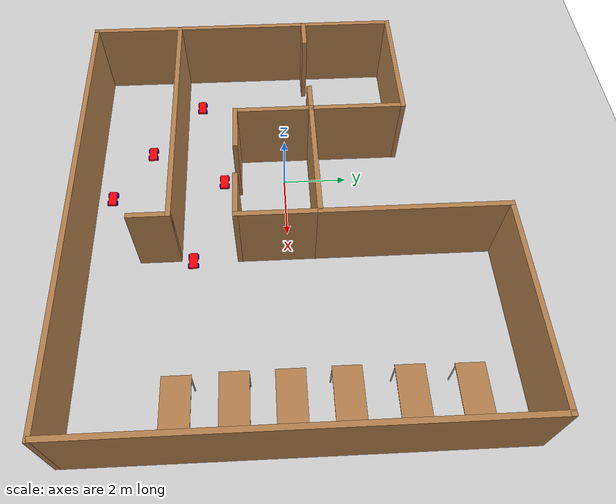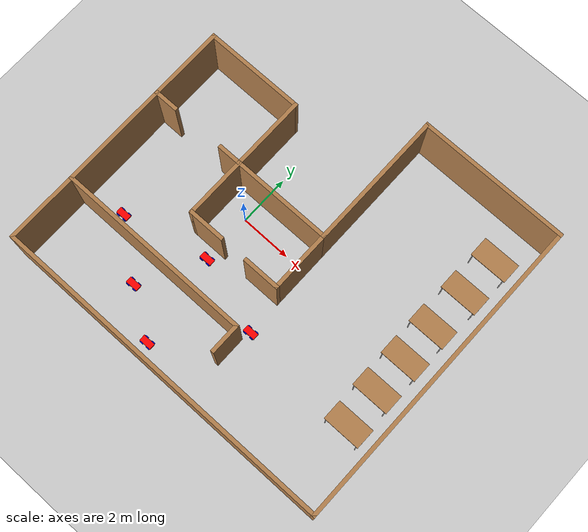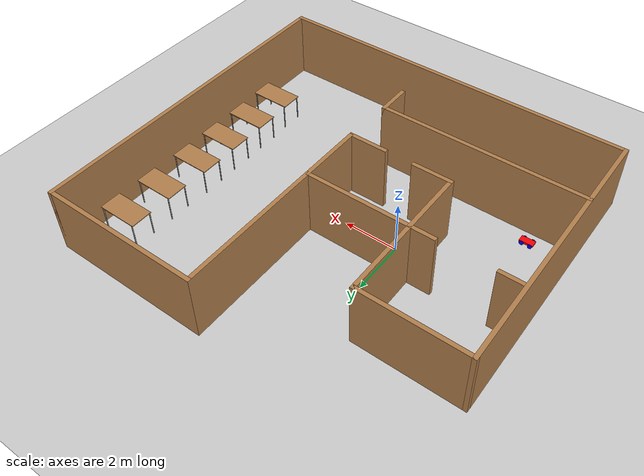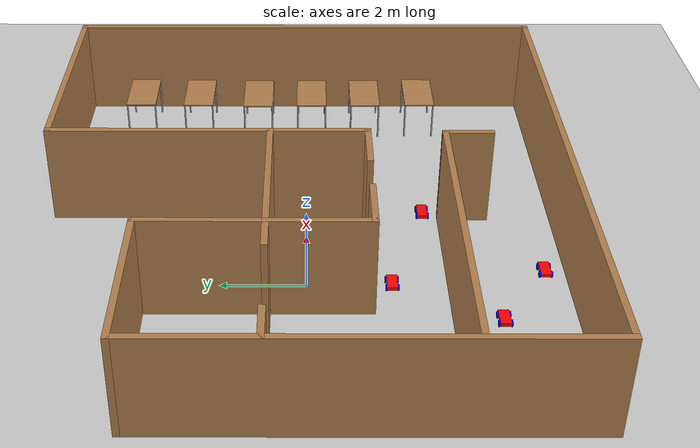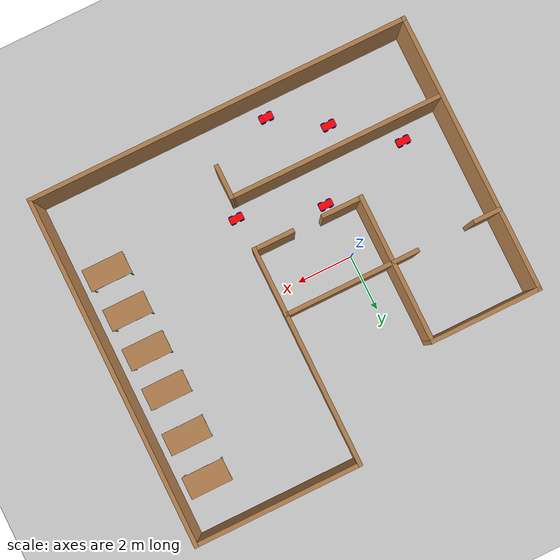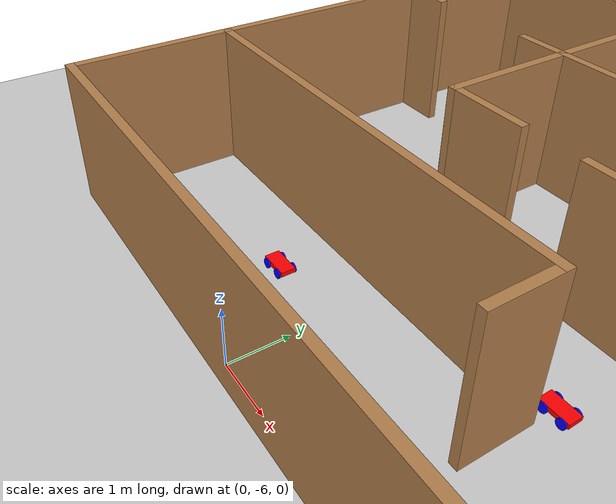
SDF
<sdf version="1.6">
 <world name="default">
  <light name="sun" type="directional">
   <pose>0 0 10 0 -0 0</pose>
   <diffuse>0.8 0.8 0.8 1</diffuse>
   <specular>0.2 0.2 0.2 1</specular>
   <attenuation>
    <range>1000</range>
    <constant>0.9</constant>
    <linear>0.01</linear>
    <quadratic>0.001</quadratic>
   </attenuation>
   <direction>-0.5 0.1 -0.9</direction>
  </light>
  <model name="ground_plane">
   <static>1</static>
   <link name="link">
    <collision name="collision">
     <geometry><plane><normal>0 0 1</normal><size>100 100</size></plane></geometry>
     <surface><friction><ode><mu>100</mu><mu2>50</mu2></ode></friction></surface>
    </collision>
    <visual name="visual">
     <cast_shadows>0</cast_shadows>
     <geometry><plane><normal>0 0 1</normal><size>100 100</size></plane></geometry>
     <material>
      <script><uri>file://media/materials/scripts/gazebo.material</uri><name>Gazebo/Grey</name></script>
     </material>
    </visual>
   </link>
  </model>
  <gravity>0 0 -9.8</gravity>
  <magnetic_field>6e-06 2.3e-05 -4.2e-05</magnetic_field>
  <atmosphere type="adiabatic"/>
  <physics name="default_physics" default="0" type="ode">
   <max_step_size>0.001</max_step_size>
   <real_time_factor>1</real_time_factor>
   <real_time_update_rate>1000</real_time_update_rate>
  </physics>
  <scene><ambient>0.4 0.4 0.4 1</ambient><background>0.7 0.7 0.7 1</background><shadows>1</shadows></scene>
  <spherical_coordinates>
   <surface_model>EARTH_WGS84</surface_model>
   <latitude_deg>0</latitude_deg>
   <longitude_deg>0</longitude_deg>
   <elevation>0</elevation>
   <heading_deg>0</heading_deg>
  </spherical_coordinates>
  <model name="my_room">
   <link name="Wall_0">
    <pose>-4.84997 3.67511 0 0 -0 3.14154</pose>
    <visual name="Wall_0_Visual">
     <pose>0 0 1.25 0 -0 0</pose>
     <geometry><box><size>4 0.15 2.5</size></box></geometry>
     <material>
      <script><uri>file://media/materials/scripts/gazebo.material</uri><name>Gazebo/Wood</name></script>
      <ambient>1 1 1 1</ambient>
      <shader type="pixel"/>
      <diffuse>1 1 1 1</diffuse>
      <specular>0.2 0.2 0.2 1</specular>
      <emissive>0 0 0 1</emissive>
     </material>
     <meta><layer>0</layer></meta>
    </visual>
    <collision name="Wall_0_Collision">
     <pose>0 0 1.25 0 -0 0</pose>
     <geometry><box><size>4 0.15 2.5</size></box></geometry>
     <surface>
      <friction>
       <ode><mu>1</mu><mu2>1</mu2><fdir1>0 0 0</fdir1><slip1>0</slip1><slip2>0</slip2></ode>
       <torsional>
        <coefficient>1</coefficient>
        <patch_radius>0</patch_radius>
        <surface_radius>0</surface_radius>
        <use_patch_radius>1</use_patch_radius>
        <ode><slip>0</slip></ode>
       </torsional>
      </friction>
      <bounce><restitution_coefficient>0</restitution_coefficient><threshold>1e+06</threshold></bounce>
      <contact>
       <collide_without_contact>0</collide_without_contact>
       <collide_without_contact_bitmask>1</collide_without_contact_bitmask>
       <collide_bitmask>1</collide_bitmask>
       <ode>
        <soft_cfm>0</soft_cfm>
        <soft_erp>0.2</soft_erp>
        <kp>1e+13</kp>
        <kd>1</kd>
        <max_vel>0.01</max_vel>
        <min_depth>0</min_depth>
       </ode>
       <bullet>
        <split_impulse>1</split_impulse>
        <split_impulse_penetration_threshold>-0.01</split_impulse_penetration_threshold>
        <soft_cfm>0</soft_cfm>
        <soft_erp>0.2</soft_erp>
        <kp>1e+13</kp>
        <kd>1</kd>
       </bullet>
      </contact>
     </surface>
    </collision>
   </link>
   <link name="Wall_1">
    <pose>-6.7749 -1.24978 0 0 0 -1.5708</pose>
    <inertial>
     <mass>1</mass>
     <inertia><ixx>1</ixx><ixy>0</ixy><ixz>0</ixz><iyy>1</iyy><iyz>0</iyz><izz>1</izz></inertia>
    </inertial>
    <visual name="Wall_1_Visual">
     <pose>0 0 1.25 0 -0 0</pose>
     <geometry><box><size>10 0.15 2.5</size></box></geometry>
     <material>
      <script><uri>file://media/materials/scripts/gazebo.material</uri><name>Gazebo/Wood</name></script>
      <ambient>1 1 0 1</ambient>
      <shader type="pixel"><normal_map>__default__</normal_map></shader>
      <diffuse>1 1 1 1</diffuse>
      <specular>0.2 0.2 0.2 1</specular>
      <emissive>0 0 0 1</emissive>
     </material>
     <meta><layer>0</layer></meta>
    </visual>
    <collision name="Wall_1_Collision">
     <pose>0 0 1.25 0 -0 0</pose>
     <geometry><box><size>10 0.15 2.5</size></box></geometry>
     <surface>
      <friction>
       <ode><mu>1</mu><mu2>1</mu2><fdir1>0 0 0</fdir1><slip1>0</slip1><slip2>0</slip2></ode>
       <torsional>
        <coefficient>1</coefficient>
        <patch_radius>0</patch_radius>
        <surface_radius>0</surface_radius>
        <use_patch_radius>1</use_patch_radius>
        <ode><slip>0</slip></ode>
       </torsional>
      </friction>
      <bounce><restitution_coefficient>0</restitution_coefficient><threshold>1e+06</threshold></bounce>
      <contact>
       <collide_without_contact>0</collide_without_contact>
       <collide_without_contact_bitmask>1</collide_without_contact_bitmask>
       <collide_bitmask>1</collide_bitmask>
       <ode>
        <soft_cfm>0</soft_cfm>
        <soft_erp>0.2</soft_erp>
        <kp>1e+13</kp>
        <kd>1</kd>
        <max_vel>0.01</max_vel>
        <min_depth>0</min_depth>
       </ode>
       <bullet>
        <split_impulse>1</split_impulse>
        <split_impulse_penetration_threshold>-0.01</split_impulse_penetration_threshold>
        <soft_cfm>0</soft_cfm>
        <soft_erp>0.2</soft_erp>
        <kp>1e+13</kp>
        <kd>1</kd>
       </bullet>
      </contact>
     </surface>
    </collision>
   </link>
   <link name="Wall_11">
    <pose>-2.92503 2.25 0 0 0 -1.5708</pose>
    <visual name="Wall_11_Visual">
     <pose>0 0 1.25 0 -0 0</pose>
     <geometry><box><size>3 0.15 2.5</size></box></geometry>
     <material>
      <script><uri>file://media/materials/scripts/gazebo.material</uri><name>Gazebo/Wood</name></script>
      <ambient>1 1 1 1</ambient>
      <shader type="pixel"/>
      <diffuse>1 1 1 1</diffuse>
      <specular>0.2 0.2 0.2 1</specular>
      <emissive>0 0 0 1</emissive>
     </material>
     <meta><layer>0</layer></meta>
    </visual>
    <collision name="Wall_11_Collision">
     <pose>0 0 1.25 0 -0 0</pose>
     <geometry><box><size>3 0.15 2.5</size></box></geometry>
     <surface>
      <friction>
       <ode><mu>1</mu><mu2>1</mu2><fdir1>0 0 0</fdir1><slip1>0</slip1><slip2>0</slip2></ode>
       <torsional>
        <coefficient>1</coefficient>
        <patch_radius>0</patch_radius>
        <surface_radius>0</surface_radius>
        <use_patch_radius>1</use_patch_radius>
        <ode><slip>0</slip></ode>
       </torsional>
      </friction>
      <bounce><restitution_coefficient>0</restitution_coefficient><threshold>1e+06</threshold></bounce>
      <contact>
       <collide_without_contact>0</collide_without_contact>
       <collide_without_contact_bitmask>1</collide_without_contact_bitmask>
       <collide_bitmask>1</collide_bitmask>
       <ode>
        <soft_cfm>0</soft_cfm>
        <soft_erp>0.2</soft_erp>
        <kp>1e+13</kp>
        <kd>1</kd>
        <max_vel>0.01</max_vel>
        <min_depth>0</min_depth>
       </ode>
       <bullet>
        <split_impulse>1</split_impulse>
        <split_impulse_penetration_threshold>-0.01</split_impulse_penetration_threshold>
        <soft_cfm>0</soft_cfm>
        <soft_erp>0.2</soft_erp>
        <kp>1e+13</kp>
        <kd>1</kd>
       </bullet>
      </contact>
     </surface>
    </collision>
   </link>
   <link name="Wall_12">
    <pose>-1.00003 0.825 0 0 -0 0</pose>
    <visual name="Wall_12_Visual">
     <pose>0 0 1.25 0 -0 0</pose>
     <geometry><box><size>4 0.15 2.5</size></box></geometry>
     <material>
      <script><uri>file://media/materials/scripts/gazebo.material</uri><name>Gazebo/Wood</name></script>
      <ambient>1 1 1 1</ambient>
      <shader type="pixel"/>
      <diffuse>1 1 1 1</diffuse>
      <specular>0.2 0.2 0.2 1</specular>
      <emissive>0 0 0 1</emissive>
     </material>
     <meta><layer>0</layer></meta>
    </visual>
    <collision name="Wall_12_Collision">
     <pose>0 0 1.25 0 -0 0</pose>
     <geometry><box><size>4 0.15 2.5</size></box></geometry>
     <surface>
      <friction>
       <ode><mu>1</mu><mu2>1</mu2><fdir1>0 0 0</fdir1><slip1>0</slip1><slip2>0</slip2></ode>
       <torsional>
        <coefficient>1</coefficient>
        <patch_radius>0</patch_radius>
        <surface_radius>0</surface_radius>
        <use_patch_radius>1</use_patch_radius>
        <ode><slip>0</slip></ode>
       </torsional>
      </friction>
      <bounce><restitution_coefficient>0</restitution_coefficient><threshold>1e+06</threshold></bounce>
      <contact>
       <collide_without_contact>0</collide_without_contact>
       <collide_without_contact_bitmask>1</collide_without_contact_bitmask>
       <collide_bitmask>1</collide_bitmask>
       <ode>
        <soft_cfm>0</soft_cfm>
        <soft_erp>0.2</soft_erp>
        <kp>1e+13</kp>
        <kd>1</kd>
        <max_vel>0.01</max_vel>
        <min_depth>0</min_depth>
       </ode>
       <bullet>
        <split_impulse>1</split_impulse>
        <split_impulse_penetration_threshold>-0.01</split_impulse_penetration_threshold>
        <soft_cfm>0</soft_cfm>
        <soft_erp>0.2</soft_erp>
        <kp>1e+13</kp>
        <kd>1</kd>
       </bullet>
      </contact>
     </surface>
    </collision>
   </link>
   <link name="Wall_13">
    <pose>0.924969 3.5 0 0 -0 1.5708</pose>
    <visual name="Wall_13_Visual">
     <pose>0 0 1.25 0 -0 0</pose>
     <geometry><box><size>5.5 0.15 2.5</size></box></geometry>
     <material>
      <script><uri>file://media/materials/scripts/gazebo.material</uri><name>Gazebo/Wood</name></script>
      <ambient>1 1 1 1</ambient>
      <shader type="pixel"/>
      <diffuse>1 1 1 1</diffuse>
      <specular>0.2 0.2 0.2 1</specular>
      <emissive>0 0 0 1</emissive>
     </material>
     <meta><layer>0</layer></meta>
    </visual>
    <collision name="Wall_13_Collision">
     <pose>0 0 1.25 0 -0 0</pose>
     <geometry><box><size>5.5 0.15 2.5</size></box></geometry>
     <surface>
      <friction>
       <ode><mu>1</mu><mu2>1</mu2><fdir1>0 0 0</fdir1><slip1>0</slip1><slip2>0</slip2></ode>
       <torsional>
        <coefficient>1</coefficient>
        <patch_radius>0</patch_radius>
        <surface_radius>0</surface_radius>
        <use_patch_radius>1</use_patch_radius>
        <ode><slip>0</slip></ode>
       </torsional>
      </friction>
      <bounce><restitution_coefficient>0</restitution_coefficient><threshold>1e+06</threshold></bounce>
      <contact>
       <collide_without_contact>0</collide_without_contact>
       <collide_without_contact_bitmask>1</collide_without_contact_bitmask>
       <collide_bitmask>1</collide_bitmask>
       <ode>
        <soft_cfm>0</soft_cfm>
        <soft_erp>0.2</soft_erp>
        <kp>1e+13</kp>
        <kd>1</kd>
        <max_vel>0.01</max_vel>
        <min_depth>0</min_depth>
       </ode>
       <bullet>
        <split_impulse>1</split_impulse>
        <split_impulse_penetration_threshold>-0.01</split_impulse_penetration_threshold>
        <soft_cfm>0</soft_cfm>
        <soft_erp>0.2</soft_erp>
        <kp>1e+13</kp>
        <kd>1</kd>
       </bullet>
      </contact>
     </surface>
    </collision>
   </link>
   <link name="Wall_14">
    <pose>3.84997 6.175 0 0 -0 0</pose>
    <inertial>
     <mass>1</mass>
     <inertia><ixx>1</ixx><ixy>0</ixy><ixz>0</ixz><iyy>1</iyy><iyz>0</iyz><izz>1</izz></inertia>
    </inertial>
    <visual name="Wall_14_Visual">
     <pose>0 0 1.25 0 -0 0</pose>
     <geometry><box><size>6 0.15 2.5</size></box></geometry>
     <material>
      <script><uri>file://media/materials/scripts/gazebo.material</uri><name>Gazebo/Wood</name></script>
      <ambient>0 1 1 1</ambient>
      <shader type="pixel"><normal_map>__default__</normal_map></shader>
      <diffuse>1 1 1 1</diffuse>
      <specular>0.2 0.2 0.2 1</specular>
      <emissive>0 0 0 1</emissive>
     </material>
     <meta><layer>0</layer></meta>
    </visual>
    <collision name="Wall_14_Collision">
     <pose>0 0 1.25 0 -0 0</pose>
     <geometry><box><size>6 0.15 2.5</size></box></geometry>
     <surface>
      <friction>
       <ode><mu>1</mu><mu2>1</mu2><fdir1>0 0 0</fdir1><slip1>0</slip1><slip2>0</slip2></ode>
       <torsional>
        <coefficient>1</coefficient>
        <patch_radius>0</patch_radius>
        <surface_radius>0</surface_radius>
        <use_patch_radius>1</use_patch_radius>
        <ode><slip>0</slip></ode>
       </torsional>
      </friction>
      <bounce><restitution_coefficient>0</restitution_coefficient><threshold>1e+06</threshold></bounce>
      <contact>
       <collide_without_contact>0</collide_without_contact>
       <collide_without_contact_bitmask>1</collide_without_contact_bitmask>
       <collide_bitmask>1</collide_bitmask>
       <ode>
        <soft_cfm>0</soft_cfm>
        <soft_erp>0.2</soft_erp>
        <kp>1e+13</kp>
        <kd>1</kd>
        <max_vel>0.01</max_vel>
        <min_depth>0</min_depth>
       </ode>
       <bullet>
        <split_impulse>1</split_impulse>
        <split_impulse_penetration_threshold>-0.01</split_impulse_penetration_threshold>
        <soft_cfm>0</soft_cfm>
        <soft_erp>0.2</soft_erp>
        <kp>1e+13</kp>
        <kd>1</kd>
       </bullet>
      </contact>
     </surface>
    </collision>
   </link>
   <link name="Wall_15">
    <pose>6.77497 0 0 0 0 -1.5708</pose>
    <inertial>
     <mass>1</mass>
     <inertia><ixx>1</ixx><ixy>0</ixy><ixz>0</ixz><iyy>1</iyy><iyz>0</iyz><izz>1</izz></inertia>
    </inertial>
    <visual name="Wall_15_Visual">
     <pose>0 0 1.25 0 -0 0</pose>
     <geometry><box><size>12.5 0.15 2.5</size></box></geometry>
     <material>
      <script><uri>file://media/materials/scripts/gazebo.material</uri><name>Gazebo/Wood</name></script>
      <ambient>0 1 0 1</ambient>
      <shader type="pixel"><normal_map>__default__</normal_map></shader>
      <diffuse>1 1 1 1</diffuse>
      <specular>0.2 0.2 0.2 1</specular>
      <emissive>0 0 0 1</emissive>
     </material>
     <meta><layer>0</layer></meta>
    </visual>
    <collision name="Wall_15_Collision">
     <pose>0 0 1.25 0 -0 0</pose>
     <geometry><box><size>12.5 0.15 2.5</size></box></geometry>
     <surface>
      <friction>
       <ode><mu>1</mu><mu2>1</mu2><fdir1>0 0 0</fdir1><slip1>0</slip1><slip2>0</slip2></ode>
       <torsional>
        <coefficient>1</coefficient>
        <patch_radius>0</patch_radius>
        <surface_radius>0</surface_radius>
        <use_patch_radius>1</use_patch_radius>
        <ode><slip>0</slip></ode>
       </torsional>
      </friction>
      <bounce><restitution_coefficient>0</restitution_coefficient><threshold>1e+06</threshold></bounce>
      <contact>
       <collide_without_contact>0</collide_without_contact>
       <collide_without_contact_bitmask>1</collide_without_contact_bitmask>
       <collide_bitmask>1</collide_bitmask>
       <ode>
        <soft_cfm>0</soft_cfm>
        <soft_erp>0.2</soft_erp>
        <kp>1e+13</kp>
        <kd>1</kd>
        <max_vel>0.01</max_vel>
        <min_depth>0</min_depth>
       </ode>
       <bullet>
        <split_impulse>1</split_impulse>
        <split_impulse_penetration_threshold>-0.01</split_impulse_penetration_threshold>
        <soft_cfm>0</soft_cfm>
        <soft_erp>0.2</soft_erp>
        <kp>1e+13</kp>
        <kd>1</kd>
       </bullet>
      </contact>
     </surface>
    </collision>
   </link>
   <link name="Wall_16">
    <pose>3.4e-05 -6.17489 0 0 -0 3.14158</pose>
    <inertial>
     <mass>1</mass>
     <inertia><ixx>1</ixx><ixy>0</ixy><ixz>0</ixz><iyy>1</iyy><iyz>0</iyz><izz>1</izz></inertia>
    </inertial>
    <visual name="Wall_16_Visual">
     <pose>0 0 1.25 0 -0 0</pose>
     <geometry><box><size>13.6999 0.15 2.5</size></box></geometry>
     <material>
      <script><uri>file://media/materials/scripts/gazebo.material</uri><name>Gazebo/Wood</name></script>
      <ambient>1 0 0 1</ambient>
      <shader type="pixel"><normal_map>__default__</normal_map></shader>
      <diffuse>1 1 1 1</diffuse>
      <specular>0.2 0.2 0.2 1</specular>
      <emissive>0 0 0 1</emissive>
     </material>
     <meta><layer>0</layer></meta>
    </visual>
    <collision name="Wall_16_Collision">
     <pose>0 0 1.25 0 -0 0</pose>
     <geometry><box><size>13.6999 0.15 2.5</size></box></geometry>
     <surface>
      <friction>
       <ode><mu>1</mu><mu2>1</mu2><fdir1>0 0 0</fdir1><slip1>0</slip1><slip2>0</slip2></ode>
       <torsional>
        <coefficient>1</coefficient>
        <patch_radius>0</patch_radius>
        <surface_radius>0</surface_radius>
        <use_patch_radius>1</use_patch_radius>
        <ode><slip>0</slip></ode>
       </torsional>
      </friction>
      <bounce><restitution_coefficient>0</restitution_coefficient><threshold>1e+06</threshold></bounce>
      <contact>
       <collide_without_contact>0</collide_without_contact>
       <collide_without_contact_bitmask>1</collide_without_contact_bitmask>
       <collide_bitmask>1</collide_bitmask>
       <ode>
        <soft_cfm>0</soft_cfm>
        <soft_erp>0.2</soft_erp>
        <kp>1e+13</kp>
        <kd>1</kd>
        <max_vel>0.01</max_vel>
        <min_depth>0</min_depth>
       </ode>
       <bullet>
        <split_impulse>1</split_impulse>
        <split_impulse_penetration_threshold>-0.01</split_impulse_penetration_threshold>
        <soft_cfm>0</soft_cfm>
        <soft_erp>0.2</soft_erp>
        <kp>1e+13</kp>
        <kd>1</kd>
       </bullet>
      </contact>
     </surface>
    </collision>
   </link>
   <link name="Wall_18">
    <pose>-3.35003 0.825 0 0 -0 3.14159</pose>
    <visual name="Wall_18_Visual">
     <pose>0 0 1.25 0 -0 0</pose>
     <geometry><box><size>1 0.15 2.5</size></box></geometry>
     <material>
      <script><uri>file://media/materials/scripts/gazebo.material</uri><name>Gazebo/Wood</name></script>
      <ambient>1 1 1 1</ambient>
      <shader type="pixel"/>
      <diffuse>1 1 1 1</diffuse>
      <specular>0.2 0.2 0.2 1</specular>
      <emissive>0 0 0 1</emissive>
     </material>
     <meta><layer>0</layer></meta>
    </visual>
    <collision name="Wall_18_Collision">
     <pose>0 0 1.25 0 -0 0</pose>
     <geometry><box><size>1 0.15 2.5</size></box></geometry>
     <surface>
      <friction>
       <ode><mu>1</mu><mu2>1</mu2><fdir1>0 0 0</fdir1><slip1>0</slip1><slip2>0</slip2></ode>
       <torsional>
        <coefficient>1</coefficient>
        <patch_radius>0</patch_radius>
        <surface_radius>0</surface_radius>
        <use_patch_radius>1</use_patch_radius>
        <ode><slip>0</slip></ode>
       </torsional>
      </friction>
      <bounce><restitution_coefficient>0</restitution_coefficient><threshold>1e+06</threshold></bounce>
      <contact>
       <collide_without_contact>0</collide_without_contact>
       <collide_without_contact_bitmask>1</collide_without_contact_bitmask>
       <collide_bitmask>1</collide_bitmask>
       <ode>
        <soft_cfm>0</soft_cfm>
        <soft_erp>0.2</soft_erp>
        <kp>1e+13</kp>
        <kd>1</kd>
        <max_vel>0.01</max_vel>
        <min_depth>0</min_depth>
       </ode>
       <bullet>
        <split_impulse>1</split_impulse>
        <split_impulse_penetration_threshold>-0.01</split_impulse_penetration_threshold>
        <soft_cfm>0</soft_cfm>
        <soft_erp>0.2</soft_erp>
        <kp>1e+13</kp>
        <kd>1</kd>
       </bullet>
      </contact>
     </surface>
    </collision>
   </link>
   <link name="Wall_21">
    <pose>-6.33323 0.80256 0 0 -0 0</pose>
    <visual name="Wall_21_Visual">
     <pose>0 0 1.25 0 -0 0</pose>
     <geometry><box><size>1 0.15 2.5</size></box></geometry>
     <material>
      <script><uri>file://media/materials/scripts/gazebo.material</uri><name>Gazebo/Wood</name></script>
      <ambient>1 1 1 1</ambient>
      <shader type="pixel"/>
      <diffuse>1 1 1 1</diffuse>
      <specular>0.2 0.2 0.2 1</specular>
      <emissive>0 0 0 1</emissive>
     </material>
     <meta><layer>0</layer></meta>
    </visual>
    <collision name="Wall_21_Collision">
     <pose>0 0 1.25 0 -0 0</pose>
     <geometry><box><size>1 0.15 2.5</size></box></geometry>
     <surface>
      <friction>
       <ode><mu>1</mu><mu2>1</mu2><fdir1>0 0 0</fdir1><slip1>0</slip1><slip2>0</slip2></ode>
       <torsional>
        <coefficient>1</coefficient>
        <patch_radius>0</patch_radius>
        <surface_radius>0</surface_radius>
        <use_patch_radius>1</use_patch_radius>
        <ode><slip>0</slip></ode>
       </torsional>
      </friction>
      <bounce><restitution_coefficient>0</restitution_coefficient><threshold>1e+06</threshold></bounce>
      <contact>
       <collide_without_contact>0</collide_without_contact>
       <collide_without_contact_bitmask>1</collide_without_contact_bitmask>
       <collide_bitmask>1</collide_bitmask>
       <ode>
        <soft_cfm>0</soft_cfm>
        <soft_erp>0.2</soft_erp>
        <kp>1e+13</kp>
        <kd>1</kd>
        <max_vel>0.01</max_vel>
        <min_depth>0</min_depth>
       </ode>
       <bullet>
        <split_impulse>1</split_impulse>
        <split_impulse_penetration_threshold>-0.01</split_impulse_penetration_threshold>
        <soft_cfm>0</soft_cfm>
        <soft_erp>0.2</soft_erp>
        <kp>1e+13</kp>
        <kd>1</kd>
       </bullet>
      </contact>
     </surface>
    </collision>
   </link>
   <link name="Wall_23">
    <pose>-2.92503 -0.35 0 0 0 -1.5708</pose>
    <visual name="Wall_23_Visual">
     <pose>0 0 1.25 0 -0 0</pose>
     <geometry><box><size>2.5 0.15 2.5</size></box></geometry>
     <material>
      <script><uri>file://media/materials/scripts/gazebo.material</uri><name>Gazebo/Wood</name></script>
      <ambient>1 1 1 1</ambient>
      <shader type="pixel"/>
      <diffuse>1 1 1 1</diffuse>
      <specular>0.2 0.2 0.2 1</specular>
      <emissive>0 0 0 1</emissive>
     </material>
     <meta><layer>0</layer></meta>
    </visual>
    <collision name="Wall_23_Collision">
     <pose>0 0 1.25 0 -0 0</pose>
     <geometry><box><size>2.5 0.15 2.5</size></box></geometry>
     <surface>
      <friction>
       <ode><mu>1</mu><mu2>1</mu2><fdir1>0 0 0</fdir1><slip1>0</slip1><slip2>0</slip2></ode>
       <torsional>
        <coefficient>1</coefficient>
        <patch_radius>0</patch_radius>
        <surface_radius>0</surface_radius>
        <use_patch_radius>1</use_patch_radius>
        <ode><slip>0</slip></ode>
       </torsional>
      </friction>
      <bounce><restitution_coefficient>0</restitution_coefficient><threshold>1e+06</threshold></bounce>
      <contact>
       <collide_without_contact>0</collide_without_contact>
       <collide_without_contact_bitmask>1</collide_without_contact_bitmask>
       <collide_bitmask>1</collide_bitmask>
       <ode>
        <soft_cfm>0</soft_cfm>
        <soft_erp>0.2</soft_erp>
        <kp>1e+13</kp>
        <kd>1</kd>
        <max_vel>0.01</max_vel>
        <min_depth>0</min_depth>
       </ode>
       <bullet>
        <split_impulse>1</split_impulse>
        <split_impulse_penetration_threshold>-0.01</split_impulse_penetration_threshold>
        <soft_cfm>0</soft_cfm>
        <soft_erp>0.2</soft_erp>
        <kp>1e+13</kp>
        <kd>1</kd>
       </bullet>
      </contact>
     </surface>
    </collision>
   </link>
   <link name="Wall_25">
    <pose>0.924969 -0.35 0 0 0 -1.5708</pose>
    <visual name="Wall_25_Visual">
     <pose>0 0 1.25 0 -0 0</pose>
     <geometry><box><size>2.5 0.15 2.5</size></box></geometry>
     <material>
      <script><uri>file://media/materials/scripts/gazebo.material</uri><name>Gazebo/Wood</name></script>
      <ambient>1 1 1 1</ambient>
      <shader type="pixel"/>
      <diffuse>1 1 1 1</diffuse>
      <specular>0.2 0.2 0.2 1</specular>
      <emissive>0 0 0 1</emissive>
     </material>
     <meta><layer>0</layer></meta>
    </visual>
    <collision name="Wall_25_Collision">
     <pose>0 0 1.25 0 -0 0</pose>
     <geometry><box><size>2.5 0.15 2.5</size></box></geometry>
     <surface>
      <friction>
       <ode><mu>1</mu><mu2>1</mu2><fdir1>0 0 0</fdir1><slip1>0</slip1><slip2>0</slip2></ode>
       <torsional>
        <coefficient>1</coefficient>
        <patch_radius>0</patch_radius>
        <surface_radius>0</surface_radius>
        <use_patch_radius>1</use_patch_radius>
        <ode><slip>0</slip></ode>
       </torsional>
      </friction>
      <bounce><restitution_coefficient>0</restitution_coefficient><threshold>1e+06</threshold></bounce>
      <contact>
       <collide_without_contact>0</collide_without_contact>
       <collide_without_contact_bitmask>1</collide_without_contact_bitmask>
       <collide_bitmask>1</collide_bitmask>
       <ode>
        <soft_cfm>0</soft_cfm>
        <soft_erp>0.2</soft_erp>
        <kp>1e+13</kp>
        <kd>1</kd>
        <max_vel>0.01</max_vel>
        <min_depth>0</min_depth>
       </ode>
       <bullet>
        <split_impulse>1</split_impulse>
        <split_impulse_penetration_threshold>-0.01</split_impulse_penetration_threshold>
        <soft_cfm>0</soft_cfm>
        <soft_erp>0.2</soft_erp>
        <kp>1e+13</kp>
        <kd>1</kd>
       </bullet>
      </contact>
     </surface>
    </collision>
   </link>
   <link name="Wall_27">
    <pose>-2.25003 -1.525 0 0 -0 0</pose>
    <visual name="Wall_27_Visual">
     <pose>0 0 1.25 0 -0 0</pose>
     <geometry><box><size>1.5 0.15 2.5</size></box></geometry>
     <material>
      <script><uri>file://media/materials/scripts/gazebo.material</uri><name>Gazebo/Wood</name></script>
      <ambient>1 1 1 1</ambient>
      <shader type="pixel"/>
      <diffuse>1 1 1 1</diffuse>
      <specular>0.2 0.2 0.2 1</specular>
      <emissive>0 0 0 1</emissive>
     </material>
     <meta><layer>0</layer></meta>
    </visual>
    <collision name="Wall_27_Collision">
     <pose>0 0 1.25 0 -0 0</pose>
     <geometry><box><size>1.5 0.15 2.5</size></box></geometry>
     <surface>
      <friction>
       <ode><mu>1</mu><mu2>1</mu2><fdir1>0 0 0</fdir1><slip1>0</slip1><slip2>0</slip2></ode>
       <torsional>
        <coefficient>1</coefficient>
        <patch_radius>0</patch_radius>
        <surface_radius>0</surface_radius>
        <use_patch_radius>1</use_patch_radius>
        <ode><slip>0</slip></ode>
       </torsional>
      </friction>
      <bounce><restitution_coefficient>0</restitution_coefficient><threshold>1e+06</threshold></bounce>
      <contact>
       <collide_without_contact>0</collide_without_contact>
       <collide_without_contact_bitmask>1</collide_without_contact_bitmask>
       <collide_bitmask>1</collide_bitmask>
       <ode>
        <soft_cfm>0</soft_cfm>
        <soft_erp>0.2</soft_erp>
        <kp>1e+13</kp>
        <kd>1</kd>
        <max_vel>0.01</max_vel>
        <min_depth>0</min_depth>
       </ode>
       <bullet>
        <split_impulse>1</split_impulse>
        <split_impulse_penetration_threshold>-0.01</split_impulse_penetration_threshold>
        <soft_cfm>0</soft_cfm>
        <soft_erp>0.2</soft_erp>
        <kp>1e+13</kp>
        <kd>1</kd>
       </bullet>
      </contact>
     </surface>
    </collision>
   </link>
   <link name="Wall_29">
    <pose>0.249969 -1.525 0 0 -0 3.14159</pose>
    <visual name="Wall_29_Visual">
     <pose>0 0 1.25 0 -0 0</pose>
     <geometry><box><size>1.5 0.15 2.5</size></box></geometry>
     <material>
      <script><uri>file://media/materials/scripts/gazebo.material</uri><name>Gazebo/Wood</name></script>
      <ambient>1 1 1 1</ambient>
      <shader type="pixel"/>
      <diffuse>1 1 1 1</diffuse>
      <specular>0.2 0.2 0.2 1</specular>
      <emissive>0 0 0 1</emissive>
     </material>
     <meta><layer>0</layer></meta>
    </visual>
    <collision name="Wall_29_Collision">
     <pose>0 0 1.25 0 -0 0</pose>
     <geometry><box><size>1.5 0.15 2.5</size></box></geometry>
     <surface>
      <friction>
       <ode><mu>1</mu><mu2>1</mu2><fdir1>0 0 0</fdir1><slip1>0</slip1><slip2>0</slip2></ode>
       <torsional>
        <coefficient>1</coefficient>
        <patch_radius>0</patch_radius>
        <surface_radius>0</surface_radius>
        <use_patch_radius>1</use_patch_radius>
        <ode><slip>0</slip></ode>
       </torsional>
      </friction>
      <bounce><restitution_coefficient>0</restitution_coefficient><threshold>1e+06</threshold></bounce>
      <contact>
       <collide_without_contact>0</collide_without_contact>
       <collide_without_contact_bitmask>1</collide_without_contact_bitmask>
       <collide_bitmask>1</collide_bitmask>
       <ode>
        <soft_cfm>0</soft_cfm>
        <soft_erp>0.2</soft_erp>
        <kp>1e+13</kp>
        <kd>1</kd>
        <max_vel>0.01</max_vel>
        <min_depth>0</min_depth>
       </ode>
       <bullet>
        <split_impulse>1</split_impulse>
        <split_impulse_penetration_threshold>-0.01</split_impulse_penetration_threshold>
        <soft_cfm>0</soft_cfm>
        <soft_erp>0.2</soft_erp>
        <kp>1e+13</kp>
        <kd>1</kd>
       </bullet>
      </contact>
     </surface>
    </collision>
   </link>
   <link name="Wall_33">
    <pose>-2.95965 -3.37852 0 0 -0 0</pose>
    <inertial>
     <mass>1</mass>
     <inertia><ixx>1</ixx><ixy>0</ixy><ixz>0</ixz><iyy>1</iyy><iyz>0</iyz><izz>1</izz></inertia>
    </inertial>
    <visual name="Wall_33_Visual">
     <pose>0 0 1.25 0 -0 0</pose>
     <geometry><box><size>7.75 0.15 2.5</size></box></geometry>
     <material>
      <script><uri>file://media/materials/scripts/gazebo.material</uri><name>Gazebo/Wood</name></script>
      <ambient>0 0 1 1</ambient>
      <shader type="pixel"><normal_map>__default__</normal_map></shader>
      <diffuse>1 1 1 1</diffuse>
      <specular>0.2 0.2 0.2 1</specular>
      <emissive>0 0 0 1</emissive>
     </material>
     <meta><layer>0</layer></meta>
    </visual>
    <collision name="Wall_33_Collision">
     <pose>0 0 1.25 0 -0 0</pose>
     <geometry><box><size>7.75 0.15 2.5</size></box></geometry>
     <surface>
      <friction>
       <ode><mu>1</mu><mu2>1</mu2><fdir1>0 0 0</fdir1><slip1>0</slip1><slip2>0</slip2></ode>
       <torsional>
        <coefficient>1</coefficient>
        <patch_radius>0</patch_radius>
        <surface_radius>0</surface_radius>
        <use_patch_radius>1</use_patch_radius>
        <ode><slip>0</slip></ode>
       </torsional>
      </friction>
      <bounce><restitution_coefficient>0</restitution_coefficient><threshold>1e+06</threshold></bounce>
      <contact>
       <collide_without_contact>0</collide_without_contact>
       <collide_without_contact_bitmask>1</collide_without_contact_bitmask>
       <collide_bitmask>1</collide_bitmask>
       <ode>
        <soft_cfm>0</soft_cfm>
        <soft_erp>0.2</soft_erp>
        <kp>1e+13</kp>
        <kd>1</kd>
        <max_vel>0.01</max_vel>
        <min_depth>0</min_depth>
       </ode>
       <bullet>
        <split_impulse>1</split_impulse>
        <split_impulse_penetration_threshold>-0.01</split_impulse_penetration_threshold>
        <soft_cfm>0</soft_cfm>
        <soft_erp>0.2</soft_erp>
        <kp>1e+13</kp>
        <kd>1</kd>
       </bullet>
      </contact>
     </surface>
    </collision>
   </link>
   <link name="Wall_34">
    <pose>0.840353 -3.92852 0 0 0 -1.5708</pose>
    <visual name="Wall_34_Visual">
     <pose>0 0 1.25 0 -0 0</pose>
     <geometry><box><size>1.25 0.15 2.5</size></box></geometry>
     <material>
      <script><uri>file://media/materials/scripts/gazebo.material</uri><name>Gazebo/Wood</name></script>
      <ambient>1 1 1 1</ambient>
      <shader type="pixel"/>
      <diffuse>1 1 1 1</diffuse>
      <specular>0.2 0.2 0.2 1</specular>
      <emissive>0 0 0 1</emissive>
     </material>
     <meta><layer>0</layer></meta>
    </visual>
    <collision name="Wall_34_Collision">
     <pose>0 0 1.25 0 -0 0</pose>
     <geometry><box><size>1.25 0.15 2.5</size></box></geometry>
     <surface>
      <friction>
       <ode><mu>1</mu><mu2>1</mu2><fdir1>0 0 0</fdir1><slip1>0</slip1><slip2>0</slip2></ode>
       <torsional>
        <coefficient>1</coefficient>
        <patch_radius>0</patch_radius>
        <surface_radius>0</surface_radius>
        <use_patch_radius>1</use_patch_radius>
        <ode><slip>0</slip></ode>
       </torsional>
      </friction>
      <bounce><restitution_coefficient>0</restitution_coefficient><threshold>1e+06</threshold></bounce>
      <contact>
       <collide_without_contact>0</collide_without_contact>
       <collide_without_contact_bitmask>1</collide_without_contact_bitmask>
       <collide_bitmask>1</collide_bitmask>
       <ode>
        <soft_cfm>0</soft_cfm>
        <soft_erp>0.2</soft_erp>
        <kp>1e+13</kp>
        <kd>1</kd>
        <max_vel>0.01</max_vel>
        <min_depth>0</min_depth>
       </ode>
       <bullet>
        <split_impulse>1</split_impulse>
        <split_impulse_penetration_threshold>-0.01</split_impulse_penetration_threshold>
        <soft_cfm>0</soft_cfm>
        <soft_erp>0.2</soft_erp>
        <kp>1e+13</kp>
        <kd>1</kd>
       </bullet>
      </contact>
     </surface>
    </collision>
   </link>
   <static>1</static>
   <pose>1.95391 0.05172 0 0 -0 0</pose>
  </model>
  <model name="table">
   <static>1</static>
   <link name="link">
    <collision name="surface">
     <pose>0 0 1 0 -0 0</pose>
     <geometry><box><size>1.5 0.8 0.03</size></box></geometry>
     <surface><friction><ode><mu>0.6</mu><mu2>0.6</mu2></ode></friction></surface>
    </collision>
    <visual name="visual1">
     <pose>0 0 1 0 -0 0</pose>
     <geometry><box><size>1.5 0.8 0.03</size></box></geometry>
     <material>
      <script><uri>file://media/materials/scripts/gazebo.material</uri><name>Gazebo/Wood</name></script>
     </material>
    </visual>
    <collision name="front_left_leg">
     <pose>0.68 0.38 0.5 0 -0 0</pose>
     <geometry><cylinder><radius>0.02</radius><length>1</length></cylinder></geometry>
    </collision>
    <visual name="front_left_leg">
     <pose>0.68 0.38 0.5 0 -0 0</pose>
     <geometry><cylinder><radius>0.02</radius><length>1</length></cylinder></geometry>
     <material>
      <script><uri>file://media/materials/scripts/gazebo.material</uri><name>Gazebo/Grey</name></script>
     </material>
    </visual>
    <collision name="front_right_leg">
     <pose>0.68 -0.38 0.5 0 -0 0</pose>
     <geometry><cylinder><radius>0.02</radius><length>1</length></cylinder></geometry>
    </collision>
    <visual name="front_right_leg">
     <pose>0.68 -0.38 0.5 0 -0 0</pose>
     <geometry><cylinder><radius>0.02</radius><length>1</length></cylinder></geometry>
     <material>
      <script><uri>file://media/materials/scripts/gazebo.material</uri><name>Gazebo/Grey</name></script>
     </material>
    </visual>
    <collision name="back_right_leg">
     <pose>-0.68 -0.38 0.5 0 -0 0</pose>
     <geometry><cylinder><radius>0.02</radius><length>1</length></cylinder></geometry>
    </collision>
    <visual name="back_right_leg">
     <pose>-0.68 -0.38 0.5 0 -0 0</pose>
     <geometry><cylinder><radius>0.02</radius><length>1</length></cylinder></geometry>
     <material>
      <script><uri>file://media/materials/scripts/gazebo.material</uri><name>Gazebo/Grey</name></script>
     </material>
    </visual>
    <collision name="back_left_leg">
     <pose>-0.68 0.38 0.5 0 -0 0</pose>
     <geometry><cylinder><radius>0.02</radius><length>1</length></cylinder></geometry>
    </collision>
    <visual name="back_left_leg">
     <pose>-0.68 0.38 0.5 0 -0 0</pose>
     <geometry><cylinder><radius>0.02</radius><length>1</length></cylinder></geometry>
     <material>
      <script><uri>file://media/materials/scripts/gazebo.material</uri><name>Gazebo/Grey</name></script>
     </material>
    </visual>
   </link>
   <pose>7.61318 4.55239 0 0 -0 0</pose>
  </model>
  <model name="table_0">
   <static>1</static>
   <link name="link">
    <collision name="surface">
     <pose>0 0 1 0 -0 0</pose>
     <geometry><box><size>1.5 0.8 0.03</size></box></geometry>
     <surface><friction><ode><mu>0.6</mu><mu2>0.6</mu2></ode></friction></surface>
    </collision>
    <visual name="visual1">
     <pose>0 0 1 0 -0 0</pose>
     <geometry><box><size>1.5 0.8 0.03</size></box></geometry>
     <material>
      <script><uri>file://media/materials/scripts/gazebo.material</uri><name>Gazebo/Wood</name></script>
     </material>
    </visual>
    <collision name="front_left_leg">
     <pose>0.68 0.38 0.5 0 -0 0</pose>
     <geometry><cylinder><radius>0.02</radius><length>1</length></cylinder></geometry>
    </collision>
    <visual name="front_left_leg">
     <pose>0.68 0.38 0.5 0 -0 0</pose>
     <geometry><cylinder><radius>0.02</radius><length>1</length></cylinder></geometry>
     <material>
      <script><uri>file://media/materials/scripts/gazebo.material</uri><name>Gazebo/Grey</name></script>
     </material>
    </visual>
    <collision name="front_right_leg">
     <pose>0.68 -0.38 0.5 0 -0 0</pose>
     <geometry><cylinder><radius>0.02</radius><length>1</length></cylinder></geometry>
    </collision>
    <visual name="front_right_leg">
     <pose>0.68 -0.38 0.5 0 -0 0</pose>
     <geometry><cylinder><radius>0.02</radius><length>1</length></cylinder></geometry>
     <material>
      <script><uri>file://media/materials/scripts/gazebo.material</uri><name>Gazebo/Grey</name></script>
     </material>
    </visual>
    <collision name="back_right_leg">
     <pose>-0.68 -0.38 0.5 0 -0 0</pose>
     <geometry><cylinder><radius>0.02</radius><length>1</length></cylinder></geometry>
    </collision>
    <visual name="back_right_leg">
     <pose>-0.68 -0.38 0.5 0 -0 0</pose>
     <geometry><cylinder><radius>0.02</radius><length>1</length></cylinder></geometry>
     <material>
      <script><uri>file://media/materials/scripts/gazebo.material</uri><name>Gazebo/Grey</name></script>
     </material>
    </visual>
    <collision name="back_left_leg">
     <pose>-0.68 0.38 0.5 0 -0 0</pose>
     <geometry><cylinder><radius>0.02</radius><length>1</length></cylinder></geometry>
    </collision>
    <visual name="back_left_leg">
     <pose>-0.68 0.38 0.5 0 -0 0</pose>
     <geometry><cylinder><radius>0.02</radius><length>1</length></cylinder></geometry>
     <material>
      <script><uri>file://media/materials/scripts/gazebo.material</uri><name>Gazebo/Grey</name></script>
     </material>
    </visual>
   </link>
   <pose>7.58433 2.97201 0 0 -0 0</pose>
  </model>
  <model name="table_1">
   <static>1</static>
   <link name="link">
    <collision name="surface">
     <pose>0 0 1 0 -0 0</pose>
     <geometry><box><size>1.5 0.8 0.03</size></box></geometry>
     <surface><friction><ode><mu>0.6</mu><mu2>0.6</mu2></ode></friction></surface>
    </collision>
    <visual name="visual1">
     <pose>0 0 1 0 -0 0</pose>
     <geometry><box><size>1.5 0.8 0.03</size></box></geometry>
     <material>
      <script><uri>file://media/materials/scripts/gazebo.material</uri><name>Gazebo/Wood</name></script>
     </material>
    </visual>
    <collision name="front_left_leg">
     <pose>0.68 0.38 0.5 0 -0 0</pose>
     <geometry><cylinder><radius>0.02</radius><length>1</length></cylinder></geometry>
    </collision>
    <visual name="front_left_leg">
     <pose>0.68 0.38 0.5 0 -0 0</pose>
     <geometry><cylinder><radius>0.02</radius><length>1</length></cylinder></geometry>
     <material>
      <script><uri>file://media/materials/scripts/gazebo.material</uri><name>Gazebo/Grey</name></script>
     </material>
    </visual>
    <collision name="front_right_leg">
     <pose>0.68 -0.38 0.5 0 -0 0</pose>
     <geometry><cylinder><radius>0.02</radius><length>1</length></cylinder></geometry>
    </collision>
    <visual name="front_right_leg">
     <pose>0.68 -0.38 0.5 0 -0 0</pose>
     <geometry><cylinder><radius>0.02</radius><length>1</length></cylinder></geometry>
     <material>
      <script><uri>file://media/materials/scripts/gazebo.material</uri><name>Gazebo/Grey</name></script>
     </material>
    </visual>
    <collision name="back_right_leg">
     <pose>-0.68 -0.38 0.5 0 -0 0</pose>
     <geometry><cylinder><radius>0.02</radius><length>1</length></cylinder></geometry>
    </collision>
    <visual name="back_right_leg">
     <pose>-0.68 -0.38 0.5 0 -0 0</pose>
     <geometry><cylinder><radius>0.02</radius><length>1</length></cylinder></geometry>
     <material>
      <script><uri>file://media/materials/scripts/gazebo.material</uri><name>Gazebo/Grey</name></script>
     </material>
    </visual>
    <collision name="back_left_leg">
     <pose>-0.68 0.38 0.5 0 -0 0</pose>
     <geometry><cylinder><radius>0.02</radius><length>1</length></cylinder></geometry>
    </collision>
    <visual name="back_left_leg">
     <pose>-0.68 0.38 0.5 0 -0 0</pose>
     <geometry><cylinder><radius>0.02</radius><length>1</length></cylinder></geometry>
     <material>
      <script><uri>file://media/materials/scripts/gazebo.material</uri><name>Gazebo/Grey</name></script>
     </material>
    </visual>
   </link>
   <pose>7.53455 1.32964 0 0 -0 0</pose>
  </model>
  <model name="table_2">
   <static>1</static>
   <link name="link">
    <collision name="surface">
     <pose>0 0 1 0 -0 0</pose>
     <geometry><box><size>1.5 0.8 0.03</size></box></geometry>
     <surface><friction><ode><mu>0.6</mu><mu2>0.6</mu2></ode></friction></surface>
    </collision>
    <visual name="visual1">
     <pose>0 0 1 0 -0 0</pose>
     <geometry><box><size>1.5 0.8 0.03</size></box></geometry>
     <material>
      <script><uri>file://media/materials/scripts/gazebo.material</uri><name>Gazebo/Wood</name></script>
     </material>
    </visual>
    <collision name="front_left_leg">
     <pose>0.68 0.38 0.5 0 -0 0</pose>
     <geometry><cylinder><radius>0.02</radius><length>1</length></cylinder></geometry>
    </collision>
    <visual name="front_left_leg">
     <pose>0.68 0.38 0.5 0 -0 0</pose>
     <geometry><cylinder><radius>0.02</radius><length>1</length></cylinder></geometry>
     <material>
      <script><uri>file://media/materials/scripts/gazebo.material</uri><name>Gazebo/Grey</name></script>
     </material>
    </visual>
    <collision name="front_right_leg">
     <pose>0.68 -0.38 0.5 0 -0 0</pose>
     <geometry><cylinder><radius>0.02</radius><length>1</length></cylinder></geometry>
    </collision>
    <visual name="front_right_leg">
     <pose>0.68 -0.38 0.5 0 -0 0</pose>
     <geometry><cylinder><radius>0.02</radius><length>1</length></cylinder></geometry>
     <material>
      <script><uri>file://media/materials/scripts/gazebo.material</uri><name>Gazebo/Grey</name></script>
     </material>
    </visual>
    <collision name="back_right_leg">
     <pose>-0.68 -0.38 0.5 0 -0 0</pose>
     <geometry><cylinder><radius>0.02</radius><length>1</length></cylinder></geometry>
    </collision>
    <visual name="back_right_leg">
     <pose>-0.68 -0.38 0.5 0 -0 0</pose>
     <geometry><cylinder><radius>0.02</radius><length>1</length></cylinder></geometry>
     <material>
      <script><uri>file://media/materials/scripts/gazebo.material</uri><name>Gazebo/Grey</name></script>
     </material>
    </visual>
    <collision name="back_left_leg">
     <pose>-0.68 0.38 0.5 0 -0 0</pose>
     <geometry><cylinder><radius>0.02</radius><length>1</length></cylinder></geometry>
    </collision>
    <visual name="back_left_leg">
     <pose>-0.68 0.38 0.5 0 -0 0</pose>
     <geometry><cylinder><radius>0.02</radius><length>1</length></cylinder></geometry>
     <material>
      <script><uri>file://media/materials/scripts/gazebo.material</uri><name>Gazebo/Grey</name></script>
     </material>
    </visual>
   </link>
   <pose>7.5511 -0.140414 0 0 -0 0</pose>
  </model>
  <model name="mybot">
   <link name="link_0">
    <pose>0 0 0.12 0 -0 0</pose>
    <inertial>
     <mass>1</mass>
     <inertia>
      <ixx>0.166667</ixx>
      <ixy>0</ixy>
      <ixz>0</ixz>
      <iyy>0.166667</iyy>
      <iyz>0</iyz>
      <izz>0.166667</izz>
     </inertia>
    </inertial>
    <visual name="visual">
     <geometry><box><size>0.5 0.25 0.08</size></box></geometry>
     <material>
      <lighting>1</lighting>
      <script><uri>file://media/materials/scripts/gazebo.material</uri><name>Gazebo/Grey</name></script>
      <shader type="pixel"><normal_map>__default__</normal_map></shader>
      <ambient>1 0 0 1</ambient>
      <diffuse>0.7 0.7 0.7 1</diffuse>
      <specular>0.01 0.01 0.01 1</specular>
      <emissive>0 0 0 1</emissive>
     </material>
    </visual>
    <collision name="collision">
     <geometry><box><size>0.5 0.25 0.08</size></box></geometry>
     <surface>
      <friction>
       <ode><mu>1</mu><mu2>1</mu2><fdir1>0 0 0</fdir1><slip1>0</slip1><slip2>0</slip2></ode>
       <torsional>
        <coefficient>1</coefficient>
        <patch_radius>0</patch_radius>
        <surface_radius>0</surface_radius>
        <use_patch_radius>1</use_patch_radius>
        <ode><slip>0</slip></ode>
       </torsional>
      </friction>
      <bounce><restitution_coefficient>0</restitution_coefficient><threshold>1e+06</threshold></bounce>
      <contact>
       <collide_without_contact>0</collide_without_contact>
       <collide_without_contact_bitmask>1</collide_without_contact_bitmask>
       <collide_bitmask>1</collide_bitmask>
       <ode>
        <soft_cfm>0</soft_cfm>
        <soft_erp>0.2</soft_erp>
        <kp>1e+13</kp>
        <kd>1</kd>
        <max_vel>0.01</max_vel>
        <min_depth>0</min_depth>
       </ode>
       <bullet>
        <split_impulse>1</split_impulse>
        <split_impulse_penetration_threshold>-0.01</split_impulse_penetration_threshold>
        <soft_cfm>0</soft_cfm>
        <soft_erp>0.2</soft_erp>
        <kp>1e+13</kp>
        <kd>1</kd>
       </bullet>
      </contact>
     </surface>
    </collision>
   </link>
   <link name="link_1_clone">
    <pose>0.15 0.14 0.09 1.571 -0 0</pose>
    <inertial>
     <mass>1</mass>
     <inertia><ixx>0.145833</ixx><ixy>0</ixy><ixz>0</ixz><iyy>0.145833</iyy><iyz>0</iyz><izz>0.125</izz></inertia>
    </inertial>
    <visual name="visual">
     <geometry><cylinder><radius>0.08</radius><length>0.03</length></cylinder></geometry>
     <material>
      <lighting>1</lighting>
      <script><uri>file://media/materials/scripts/gazebo.material</uri><name>Gazebo/Grey</name></script>
      <shader type="pixel"><normal_map>__default__</normal_map></shader>
      <ambient>0 0 1 1</ambient>
      <diffuse>0.7 0.7 0.7 1</diffuse>
      <specular>0.01 0.01 0.01 1</specular>
      <emissive>0 0 0 1</emissive>
     </material>
    </visual>
    <collision name="collision">
     <geometry><cylinder><radius>0.08</radius><length>0.03</length></cylinder></geometry>
     <surface>
      <friction>
       <ode><mu>1</mu><mu2>1</mu2><fdir1>0 0 0</fdir1><slip1>0</slip1><slip2>0</slip2></ode>
       <torsional>
        <coefficient>1</coefficient>
        <patch_radius>0</patch_radius>
        <surface_radius>0</surface_radius>
        <use_patch_radius>1</use_patch_radius>
        <ode><slip>0</slip></ode>
       </torsional>
      </friction>
      <bounce><restitution_coefficient>0</restitution_coefficient><threshold>1e+06</threshold></bounce>
      <contact>
       <collide_without_contact>0</collide_without_contact>
       <collide_without_contact_bitmask>1</collide_without_contact_bitmask>
       <collide_bitmask>1</collide_bitmask>
       <ode>
        <soft_cfm>0</soft_cfm>
        <soft_erp>0.2</soft_erp>
        <kp>1e+13</kp>
        <kd>1</kd>
        <max_vel>0.01</max_vel>
        <min_depth>0</min_depth>
       </ode>
       <bullet>
        <split_impulse>1</split_impulse>
        <split_impulse_penetration_threshold>-0.01</split_impulse_penetration_threshold>
        <soft_cfm>0</soft_cfm>
        <soft_erp>0.2</soft_erp>
        <kp>1e+13</kp>
        <kd>1</kd>
       </bullet>
      </contact>
     </surface>
    </collision>
   </link>
   <link name="link_1_clone_clone">
    <pose>-0.15 0.14 0.09 1.571 -0 0</pose>
    <inertial>
     <mass>1</mass>
     <inertia><ixx>0.145833</ixx><ixy>0</ixy><ixz>0</ixz><iyy>0.145833</iyy><iyz>0</iyz><izz>0.125</izz></inertia>
    </inertial>
    <visual name="visual">
     <geometry><cylinder><radius>0.08</radius><length>0.03</length></cylinder></geometry>
     <material>
      <lighting>1</lighting>
      <script><uri>file://media/materials/scripts/gazebo.material</uri><name>Gazebo/Grey</name></script>
      <shader type="pixel"><normal_map>__default__</normal_map></shader>
      <ambient>0 0 1 1</ambient>
      <diffuse>0.7 0.7 0.7 1</diffuse>
      <specular>0.01 0.01 0.01 1</specular>
      <emissive>0 0 0 1</emissive>
     </material>
    </visual>
    <collision name="collision">
     <geometry><cylinder><radius>0.08</radius><length>0.03</length></cylinder></geometry>
     <surface>
      <friction>
       <ode><mu>1</mu><mu2>1</mu2><fdir1>0 0 0</fdir1><slip1>0</slip1><slip2>0</slip2></ode>
       <torsional>
        <coefficient>1</coefficient>
        <patch_radius>0</patch_radius>
        <surface_radius>0</surface_radius>
        <use_patch_radius>1</use_patch_radius>
        <ode><slip>0</slip></ode>
       </torsional>
      </friction>
      <bounce><restitution_coefficient>0</restitution_coefficient><threshold>1e+06</threshold></bounce>
      <contact>
       <collide_without_contact>0</collide_without_contact>
       <collide_without_contact_bitmask>1</collide_without_contact_bitmask>
       <collide_bitmask>1</collide_bitmask>
       <ode>
        <soft_cfm>0</soft_cfm>
        <soft_erp>0.2</soft_erp>
        <kp>1e+13</kp>
        <kd>1</kd>
        <max_vel>0.01</max_vel>
        <min_depth>0</min_depth>
       </ode>
       <bullet>
        <split_impulse>1</split_impulse>
        <split_impulse_penetration_threshold>-0.01</split_impulse_penetration_threshold>
        <soft_cfm>0</soft_cfm>
        <soft_erp>0.2</soft_erp>
        <kp>1e+13</kp>
        <kd>1</kd>
       </bullet>
      </contact>
     </surface>
    </collision>
   </link>
   <link name="link_1_clone_clone_0">
    <pose>-0.15 -0.14 0.09 1.571 -0 0</pose>
    <inertial>
     <mass>1</mass>
     <inertia><ixx>0.145833</ixx><ixy>0</ixy><ixz>0</ixz><iyy>0.145833</iyy><iyz>0</iyz><izz>0.125</izz></inertia>
    </inertial>
    <visual name="visual">
     <geometry><cylinder><radius>0.08</radius><length>0.03</length></cylinder></geometry>
     <material>
      <lighting>1</lighting>
      <script><uri>file://media/materials/scripts/gazebo.material</uri><name>Gazebo/Grey</name></script>
      <shader type="pixel"><normal_map>__default__</normal_map></shader>
      <ambient>0 0 1 1</ambient>
      <diffuse>0.7 0.7 0.7 1</diffuse>
      <specular>0.01 0.01 0.01 1</specular>
      <emissive>0 0 0 1</emissive>
     </material>
    </visual>
    <collision name="collision">
     <geometry><cylinder><radius>0.08</radius><length>0.03</length></cylinder></geometry>
     <surface>
      <friction>
       <ode><mu>1</mu><mu2>1</mu2><fdir1>0 0 0</fdir1><slip1>0</slip1><slip2>0</slip2></ode>
       <torsional>
        <coefficient>1</coefficient>
        <patch_radius>0</patch_radius>
        <surface_radius>0</surface_radius>
        <use_patch_radius>1</use_patch_radius>
        <ode><slip>0</slip></ode>
       </torsional>
      </friction>
      <bounce><restitution_coefficient>0</restitution_coefficient><threshold>1e+06</threshold></bounce>
      <contact>
       <collide_without_contact>0</collide_without_contact>
       <collide_without_contact_bitmask>1</collide_without_contact_bitmask>
       <collide_bitmask>1</collide_bitmask>
       <ode>
        <soft_cfm>0</soft_cfm>
        <soft_erp>0.2</soft_erp>
        <kp>1e+13</kp>
        <kd>1</kd>
        <max_vel>0.01</max_vel>
        <min_depth>0</min_depth>
       </ode>
       <bullet>
        <split_impulse>1</split_impulse>
        <split_impulse_penetration_threshold>-0.01</split_impulse_penetration_threshold>
        <soft_cfm>0</soft_cfm>
        <soft_erp>0.2</soft_erp>
        <kp>1e+13</kp>
        <kd>1</kd>
       </bullet>
      </contact>
     </surface>
    </collision>
   </link>
   <link name="link_1_clone_clone_1">
    <pose>0.15 -0.14 0.09 1.571 -0 0</pose>
    <inertial>
     <mass>1</mass>
     <inertia><ixx>0.145833</ixx><ixy>0</ixy><ixz>0</ixz><iyy>0.145833</iyy><iyz>0</iyz><izz>0.125</izz></inertia>
    </inertial>
    <visual name="visual">
     <geometry><cylinder><radius>0.08</radius><length>0.03</length></cylinder></geometry>
     <material>
      <lighting>1</lighting>
      <script><uri>file://media/materials/scripts/gazebo.material</uri><name>Gazebo/Grey</name></script>
      <shader type="pixel"><normal_map>__default__</normal_map></shader>
      <ambient>0 0 1 1</ambient>
      <diffuse>0.7 0.7 0.7 1</diffuse>
      <specular>0.01 0.01 0.01 1</specular>
      <emissive>0 0 0 1</emissive>
     </material>
    </visual>
    <collision name="collision">
     <geometry><cylinder><radius>0.08</radius><length>0.03</length></cylinder></geometry>
     <surface>
      <friction>
       <ode><mu>1</mu><mu2>1</mu2><fdir1>0 0 0</fdir1><slip1>0</slip1><slip2>0</slip2></ode>
       <torsional>
        <coefficient>1</coefficient>
        <patch_radius>0</patch_radius>
        <surface_radius>0</surface_radius>
        <use_patch_radius>1</use_patch_radius>
        <ode><slip>0</slip></ode>
       </torsional>
      </friction>
      <bounce><restitution_coefficient>0</restitution_coefficient><threshold>1e+06</threshold></bounce>
      <contact>
       <collide_without_contact>0</collide_without_contact>
       <collide_without_contact_bitmask>1</collide_without_contact_bitmask>
       <collide_bitmask>1</collide_bitmask>
       <ode>
        <soft_cfm>0</soft_cfm>
        <soft_erp>0.2</soft_erp>
        <kp>1e+13</kp>
        <kd>1</kd>
        <max_vel>0.01</max_vel>
        <min_depth>0</min_depth>
       </ode>
       <bullet>
        <split_impulse>1</split_impulse>
        <split_impulse_penetration_threshold>-0.01</split_impulse_penetration_threshold>
        <soft_cfm>0</soft_cfm>
        <soft_erp>0.2</soft_erp>
        <kp>1e+13</kp>
        <kd>1</kd>
       </bullet>
      </contact>
     </surface>
    </collision>
   </link>
   <joint name="link_0_JOINT_0" type="revolute">
    <parent>link_0</parent>
    <child>link_1_clone</child>
    <axis>
     <xyz>0 0 1</xyz>
     <use_parent_model_frame>0</use_parent_model_frame>
     <limit>
      <lower>-1.79769e+308</lower>
      <upper>1.79769e+308</upper>
      <effort>-1</effort>
      <velocity>-1</velocity>
     </limit>
     <dynamics>
      <spring_reference>0</spring_reference>
      <spring_stiffness>0</spring_stiffness>
      <damping>0</damping>
      <friction>0</friction>
     </dynamics>
    </axis>
    <physics>
     <ode><limit><cfm>0</cfm><erp>0.2</erp></limit><suspension><cfm>0</cfm><erp>0.2</erp></suspension></ode>
    </physics>
   </joint>
   <joint name="link_0_JOINT_1" type="revolute">
    <parent>link_0</parent>
    <child>link_1_clone_clone</child>
    <axis>
     <xyz>0 0 1</xyz>
     <use_parent_model_frame>0</use_parent_model_frame>
     <limit>
      <lower>-1.79769e+308</lower>
      <upper>1.79769e+308</upper>
      <effort>-1</effort>
      <velocity>-1</velocity>
     </limit>
     <dynamics>
      <spring_reference>0</spring_reference>
      <spring_stiffness>0</spring_stiffness>
      <damping>0</damping>
      <friction>0</friction>
     </dynamics>
    </axis>
    <physics>
     <ode><limit><cfm>0</cfm><erp>0.2</erp></limit><suspension><cfm>0</cfm><erp>0.2</erp></suspension></ode>
    </physics>
   </joint>
   <joint name="link_0_JOINT_2" type="revolute">
    <parent>link_0</parent>
    <child>link_1_clone_clone_1</child>
    <axis>
     <xyz>0 0 1</xyz>
     <use_parent_model_frame>0</use_parent_model_frame>
     <limit>
      <lower>-1.79769e+308</lower>
      <upper>1.79769e+308</upper>
      <effort>-1</effort>
      <velocity>-1</velocity>
     </limit>
     <dynamics>
      <spring_reference>0</spring_reference>
      <spring_stiffness>0</spring_stiffness>
      <damping>0</damping>
      <friction>0</friction>
     </dynamics>
    </axis>
    <physics>
     <ode><limit><cfm>0</cfm><erp>0.2</erp></limit><suspension><cfm>0</cfm><erp>0.2</erp></suspension></ode>
    </physics>
   </joint>
   <joint name="link_0_JOINT_3" type="revolute">
    <parent>link_0</parent>
    <child>link_1_clone_clone_0</child>
    <axis>
     <xyz>0 0 1</xyz>
     <use_parent_model_frame>0</use_parent_model_frame>
     <limit>
      <lower>-1.79769e+308</lower>
      <upper>1.79769e+308</upper>
      <effort>-1</effort>
      <velocity>-1</velocity>
     </limit>
     <dynamics>
      <spring_reference>0</spring_reference>
      <spring_stiffness>0</spring_stiffness>
      <damping>0</damping>
      <friction>0</friction>
     </dynamics>
    </axis>
    <physics>
     <ode><limit><cfm>0</cfm><erp>0.2</erp></limit><suspension><cfm>0</cfm><erp>0.2</erp></suspension></ode>
    </physics>
   </joint>
   <static>0</static>
   <pose>-3.36192 -2.7761 -0.009997 -1e-06 0 0.011058</pose>
  </model>
  <model name="mybot_0">
   <link name="link_0">
    <pose>0 0 0.12 0 -0 0</pose>
    <inertial>
     <mass>1</mass>
     <inertia>
      <ixx>0.166667</ixx>
      <ixy>0</ixy>
      <ixz>0</ixz>
      <iyy>0.166667</iyy>
      <iyz>0</iyz>
      <izz>0.166667</izz>
     </inertia>
    </inertial>
    <visual name="visual">
     <geometry><box><size>0.5 0.25 0.08</size></box></geometry>
     <material>
      <lighting>1</lighting>
      <script><uri>file://media/materials/scripts/gazebo.material</uri><name>Gazebo/Grey</name></script>
      <shader type="pixel"><normal_map>__default__</normal_map></shader>
      <ambient>1 0 0 1</ambient>
      <diffuse>0.7 0.7 0.7 1</diffuse>
      <specular>0.01 0.01 0.01 1</specular>
      <emissive>0 0 0 1</emissive>
     </material>
    </visual>
    <collision name="collision">
     <geometry><box><size>0.5 0.25 0.08</size></box></geometry>
     <surface>
      <friction>
       <ode><mu>1</mu><mu2>1</mu2><fdir1>0 0 0</fdir1><slip1>0</slip1><slip2>0</slip2></ode>
       <torsional>
        <coefficient>1</coefficient>
        <patch_radius>0</patch_radius>
        <surface_radius>0</surface_radius>
        <use_patch_radius>1</use_patch_radius>
        <ode><slip>0</slip></ode>
       </torsional>
      </friction>
      <bounce><restitution_coefficient>0</restitution_coefficient><threshold>1e+06</threshold></bounce>
      <contact>
       <collide_without_contact>0</collide_without_contact>
       <collide_without_contact_bitmask>1</collide_without_contact_bitmask>
       <collide_bitmask>1</collide_bitmask>
       <ode>
        <soft_cfm>0</soft_cfm>
        <soft_erp>0.2</soft_erp>
        <kp>1e+13</kp>
        <kd>1</kd>
        <max_vel>0.01</max_vel>
        <min_depth>0</min_depth>
       </ode>
       <bullet>
        <split_impulse>1</split_impulse>
        <split_impulse_penetration_threshold>-0.01</split_impulse_penetration_threshold>
        <soft_cfm>0</soft_cfm>
        <soft_erp>0.2</soft_erp>
        <kp>1e+13</kp>
        <kd>1</kd>
       </bullet>
      </contact>
     </surface>
    </collision>
   </link>
   <link name="link_1_clone">
    <pose>0.15 0.14 0.09 1.571 -0 0</pose>
    <inertial>
     <mass>1</mass>
     <inertia><ixx>0.145833</ixx><ixy>0</ixy><ixz>0</ixz><iyy>0.145833</iyy><iyz>0</iyz><izz>0.125</izz></inertia>
    </inertial>
    <visual name="visual">
     <geometry><cylinder><radius>0.08</radius><length>0.03</length></cylinder></geometry>
     <material>
      <lighting>1</lighting>
      <script><uri>file://media/materials/scripts/gazebo.material</uri><name>Gazebo/Grey</name></script>
      <shader type="pixel"><normal_map>__default__</normal_map></shader>
      <ambient>0 0 1 1</ambient>
      <diffuse>0.7 0.7 0.7 1</diffuse>
      <specular>0.01 0.01 0.01 1</specular>
      <emissive>0 0 0 1</emissive>
     </material>
    </visual>
    <collision name="collision">
     <geometry><cylinder><radius>0.08</radius><length>0.03</length></cylinder></geometry>
     <surface>
      <friction>
       <ode><mu>1</mu><mu2>1</mu2><fdir1>0 0 0</fdir1><slip1>0</slip1><slip2>0</slip2></ode>
       <torsional>
        <coefficient>1</coefficient>
        <patch_radius>0</patch_radius>
        <surface_radius>0</surface_radius>
        <use_patch_radius>1</use_patch_radius>
        <ode><slip>0</slip></ode>
       </torsional>
      </friction>
      <bounce><restitution_coefficient>0</restitution_coefficient><threshold>1e+06</threshold></bounce>
      <contact>
       <collide_without_contact>0</collide_without_contact>
       <collide_without_contact_bitmask>1</collide_without_contact_bitmask>
       <collide_bitmask>1</collide_bitmask>
       <ode>
        <soft_cfm>0</soft_cfm>
        <soft_erp>0.2</soft_erp>
        <kp>1e+13</kp>
        <kd>1</kd>
        <max_vel>0.01</max_vel>
        <min_depth>0</min_depth>
       </ode>
       <bullet>
        <split_impulse>1</split_impulse>
        <split_impulse_penetration_threshold>-0.01</split_impulse_penetration_threshold>
        <soft_cfm>0</soft_cfm>
        <soft_erp>0.2</soft_erp>
        <kp>1e+13</kp>
        <kd>1</kd>
       </bullet>
      </contact>
     </surface>
    </collision>
   </link>
   <link name="link_1_clone_clone">
    <pose>-0.15 0.14 0.09 1.571 -0 0</pose>
    <inertial>
     <mass>1</mass>
     <inertia><ixx>0.145833</ixx><ixy>0</ixy><ixz>0</ixz><iyy>0.145833</iyy><iyz>0</iyz><izz>0.125</izz></inertia>
    </inertial>
    <visual name="visual">
     <geometry><cylinder><radius>0.08</radius><length>0.03</length></cylinder></geometry>
     <material>
      <lighting>1</lighting>
      <script><uri>file://media/materials/scripts/gazebo.material</uri><name>Gazebo/Grey</name></script>
      <shader type="pixel"><normal_map>__default__</normal_map></shader>
      <ambient>0 0 1 1</ambient>
      <diffuse>0.7 0.7 0.7 1</diffuse>
      <specular>0.01 0.01 0.01 1</specular>
      <emissive>0 0 0 1</emissive>
     </material>
    </visual>
    <collision name="collision">
     <geometry><cylinder><radius>0.08</radius><length>0.03</length></cylinder></geometry>
     <surface>
      <friction>
       <ode><mu>1</mu><mu2>1</mu2><fdir1>0 0 0</fdir1><slip1>0</slip1><slip2>0</slip2></ode>
       <torsional>
        <coefficient>1</coefficient>
        <patch_radius>0</patch_radius>
        <surface_radius>0</surface_radius>
        <use_patch_radius>1</use_patch_radius>
        <ode><slip>0</slip></ode>
       </torsional>
      </friction>
      <bounce><restitution_coefficient>0</restitution_coefficient><threshold>1e+06</threshold></bounce>
      <contact>
       <collide_without_contact>0</collide_without_contact>
       <collide_without_contact_bitmask>1</collide_without_contact_bitmask>
       <collide_bitmask>1</collide_bitmask>
       <ode>
        <soft_cfm>0</soft_cfm>
        <soft_erp>0.2</soft_erp>
        <kp>1e+13</kp>
        <kd>1</kd>
        <max_vel>0.01</max_vel>
        <min_depth>0</min_depth>
       </ode>
       <bullet>
        <split_impulse>1</split_impulse>
        <split_impulse_penetration_threshold>-0.01</split_impulse_penetration_threshold>
        <soft_cfm>0</soft_cfm>
        <soft_erp>0.2</soft_erp>
        <kp>1e+13</kp>
        <kd>1</kd>
       </bullet>
      </contact>
     </surface>
    </collision>
   </link>
   <link name="link_1_clone_clone_0">
    <pose>-0.15 -0.14 0.09 1.571 -0 0</pose>
    <inertial>
     <mass>1</mass>
     <inertia><ixx>0.145833</ixx><ixy>0</ixy><ixz>0</ixz><iyy>0.145833</iyy><iyz>0</iyz><izz>0.125</izz></inertia>
    </inertial>
    <visual name="visual">
     <geometry><cylinder><radius>0.08</radius><length>0.03</length></cylinder></geometry>
     <material>
      <lighting>1</lighting>
      <script><uri>file://media/materials/scripts/gazebo.material</uri><name>Gazebo/Grey</name></script>
      <shader type="pixel"><normal_map>__default__</normal_map></shader>
      <ambient>0 0 1 1</ambient>
      <diffuse>0.7 0.7 0.7 1</diffuse>
      <specular>0.01 0.01 0.01 1</specular>
      <emissive>0 0 0 1</emissive>
     </material>
    </visual>
    <collision name="collision">
     <geometry><cylinder><radius>0.08</radius><length>0.03</length></cylinder></geometry>
     <surface>
      <friction>
       <ode><mu>1</mu><mu2>1</mu2><fdir1>0 0 0</fdir1><slip1>0</slip1><slip2>0</slip2></ode>
       <torsional>
        <coefficient>1</coefficient>
        <patch_radius>0</patch_radius>
        <surface_radius>0</surface_radius>
        <use_patch_radius>1</use_patch_radius>
        <ode><slip>0</slip></ode>
       </torsional>
      </friction>
      <bounce><restitution_coefficient>0</restitution_coefficient><threshold>1e+06</threshold></bounce>
      <contact>
       <collide_without_contact>0</collide_without_contact>
       <collide_without_contact_bitmask>1</collide_without_contact_bitmask>
       <collide_bitmask>1</collide_bitmask>
       <ode>
        <soft_cfm>0</soft_cfm>
        <soft_erp>0.2</soft_erp>
        <kp>1e+13</kp>
        <kd>1</kd>
        <max_vel>0.01</max_vel>
        <min_depth>0</min_depth>
       </ode>
       <bullet>
        <split_impulse>1</split_impulse>
        <split_impulse_penetration_threshold>-0.01</split_impulse_penetration_threshold>
        <soft_cfm>0</soft_cfm>
        <soft_erp>0.2</soft_erp>
        <kp>1e+13</kp>
        <kd>1</kd>
       </bullet>
      </contact>
     </surface>
    </collision>
   </link>
   <link name="link_1_clone_clone_1">
    <pose>0.15 -0.14 0.09 1.571 -0 0</pose>
    <inertial>
     <mass>1</mass>
     <inertia><ixx>0.145833</ixx><ixy>0</ixy><ixz>0</ixz><iyy>0.145833</iyy><iyz>0</iyz><izz>0.125</izz></inertia>
    </inertial>
    <visual name="visual">
     <geometry><cylinder><radius>0.08</radius><length>0.03</length></cylinder></geometry>
     <material>
      <lighting>1</lighting>
      <script><uri>file://media/materials/scripts/gazebo.material</uri><name>Gazebo/Grey</name></script>
      <shader type="pixel"><normal_map>__default__</normal_map></shader>
      <ambient>0 0 1 1</ambient>
      <diffuse>0.7 0.7 0.7 1</diffuse>
      <specular>0.01 0.01 0.01 1</specular>
      <emissive>0 0 0 1</emissive>
     </material>
    </visual>
    <collision name="collision">
     <geometry><cylinder><radius>0.08</radius><length>0.03</length></cylinder></geometry>
     <surface>
      <friction>
       <ode><mu>1</mu><mu2>1</mu2><fdir1>0 0 0</fdir1><slip1>0</slip1><slip2>0</slip2></ode>
       <torsional>
        <coefficient>1</coefficient>
        <patch_radius>0</patch_radius>
        <surface_radius>0</surface_radius>
        <use_patch_radius>1</use_patch_radius>
        <ode><slip>0</slip></ode>
       </torsional>
      </friction>
      <bounce><restitution_coefficient>0</restitution_coefficient><threshold>1e+06</threshold></bounce>
      <contact>
       <collide_without_contact>0</collide_without_contact>
       <collide_without_contact_bitmask>1</collide_without_contact_bitmask>
       <collide_bitmask>1</collide_bitmask>
       <ode>
        <soft_cfm>0</soft_cfm>
        <soft_erp>0.2</soft_erp>
        <kp>1e+13</kp>
        <kd>1</kd>
        <max_vel>0.01</max_vel>
        <min_depth>0</min_depth>
       </ode>
       <bullet>
        <split_impulse>1</split_impulse>
        <split_impulse_penetration_threshold>-0.01</split_impulse_penetration_threshold>
        <soft_cfm>0</soft_cfm>
        <soft_erp>0.2</soft_erp>
        <kp>1e+13</kp>
        <kd>1</kd>
       </bullet>
      </contact>
     </surface>
    </collision>
   </link>
   <joint name="link_0_JOINT_0" type="revolute">
    <parent>link_0</parent>
    <child>link_1_clone</child>
    <axis>
     <xyz>0 0 1</xyz>
     <use_parent_model_frame>0</use_parent_model_frame>
     <limit>
      <lower>-1.79769e+308</lower>
      <upper>1.79769e+308</upper>
      <effort>-1</effort>
      <velocity>-1</velocity>
     </limit>
     <dynamics>
      <spring_reference>0</spring_reference>
      <spring_stiffness>0</spring_stiffness>
      <damping>0</damping>
      <friction>0</friction>
     </dynamics>
    </axis>
    <physics>
     <ode><limit><cfm>0</cfm><erp>0.2</erp></limit><suspension><cfm>0</cfm><erp>0.2</erp></suspension></ode>
    </physics>
   </joint>
   <joint name="link_0_JOINT_1" type="revolute">
    <parent>link_0</parent>
    <child>link_1_clone_clone</child>
    <axis>
     <xyz>0 0 1</xyz>
     <use_parent_model_frame>0</use_parent_model_frame>
     <limit>
      <lower>-1.79769e+308</lower>
      <upper>1.79769e+308</upper>
      <effort>-1</effort>
      <velocity>-1</velocity>
     </limit>
     <dynamics>
      <spring_reference>0</spring_reference>
      <spring_stiffness>0</spring_stiffness>
      <damping>0</damping>
      <friction>0</friction>
     </dynamics>
    </axis>
    <physics>
     <ode><limit><cfm>0</cfm><erp>0.2</erp></limit><suspension><cfm>0</cfm><erp>0.2</erp></suspension></ode>
    </physics>
   </joint>
   <joint name="link_0_JOINT_2" type="revolute">
    <parent>link_0</parent>
    <child>link_1_clone_clone_1</child>
    <axis>
     <xyz>0 0 1</xyz>
     <use_parent_model_frame>0</use_parent_model_frame>
     <limit>
      <lower>-1.79769e+308</lower>
      <upper>1.79769e+308</upper>
      <effort>-1</effort>
      <velocity>-1</velocity>
     </limit>
     <dynamics>
      <spring_reference>0</spring_reference>
      <spring_stiffness>0</spring_stiffness>
      <damping>0</damping>
      <friction>0</friction>
     </dynamics>
    </axis>
    <physics>
     <ode><limit><cfm>0</cfm><erp>0.2</erp></limit><suspension><cfm>0</cfm><erp>0.2</erp></suspension></ode>
    </physics>
   </joint>
   <joint name="link_0_JOINT_3" type="revolute">
    <parent>link_0</parent>
    <child>link_1_clone_clone_0</child>
    <axis>
     <xyz>0 0 1</xyz>
     <use_parent_model_frame>0</use_parent_model_frame>
     <limit>
      <lower>-1.79769e+308</lower>
      <upper>1.79769e+308</upper>
      <effort>-1</effort>
      <velocity>-1</velocity>
     </limit>
     <dynamics>
      <spring_reference>0</spring_reference>
      <spring_stiffness>0</spring_stiffness>
      <damping>0</damping>
      <friction>0</friction>
     </dynamics>
    </axis>
    <physics>
     <ode><limit><cfm>0</cfm><erp>0.2</erp></limit><suspension><cfm>0</cfm><erp>0.2</erp></suspension></ode>
    </physics>
   </joint>
   <static>0</static>
   <pose>-0.014512 -1.97168 -0.009998 0 -8e-06 0.004899</pose>
  </model>
  <model name="mybot_1">
   <link name="link_0">
    <pose>0 0 0.12 0 -0 0</pose>
    <inertial>
     <mass>1</mass>
     <inertia>
      <ixx>0.166667</ixx>
      <ixy>0</ixy>
      <ixz>0</ixz>
      <iyy>0.166667</iyy>
      <iyz>0</iyz>
      <izz>0.166667</izz>
     </inertia>
    </inertial>
    <visual name="visual">
     <geometry><box><size>0.5 0.25 0.08</size></box></geometry>
     <material>
      <lighting>1</lighting>
      <script><uri>file://media/materials/scripts/gazebo.material</uri><name>Gazebo/Grey</name></script>
      <shader type="pixel"><normal_map>__default__</normal_map></shader>
      <ambient>1 0 0 1</ambient>
      <diffuse>0.7 0.7 0.7 1</diffuse>
      <specular>0.01 0.01 0.01 1</specular>
      <emissive>0 0 0 1</emissive>
     </material>
    </visual>
    <collision name="collision">
     <geometry><box><size>0.5 0.25 0.08</size></box></geometry>
     <surface>
      <friction>
       <ode><mu>1</mu><mu2>1</mu2><fdir1>0 0 0</fdir1><slip1>0</slip1><slip2>0</slip2></ode>
       <torsional>
        <coefficient>1</coefficient>
        <patch_radius>0</patch_radius>
        <surface_radius>0</surface_radius>
        <use_patch_radius>1</use_patch_radius>
        <ode><slip>0</slip></ode>
       </torsional>
      </friction>
      <bounce><restitution_coefficient>0</restitution_coefficient><threshold>1e+06</threshold></bounce>
      <contact>
       <collide_without_contact>0</collide_without_contact>
       <collide_without_contact_bitmask>1</collide_without_contact_bitmask>
       <collide_bitmask>1</collide_bitmask>
       <ode>
        <soft_cfm>0</soft_cfm>
        <soft_erp>0.2</soft_erp>
        <kp>1e+13</kp>
        <kd>1</kd>
        <max_vel>0.01</max_vel>
        <min_depth>0</min_depth>
       </ode>
       <bullet>
        <split_impulse>1</split_impulse>
        <split_impulse_penetration_threshold>-0.01</split_impulse_penetration_threshold>
        <soft_cfm>0</soft_cfm>
        <soft_erp>0.2</soft_erp>
        <kp>1e+13</kp>
        <kd>1</kd>
       </bullet>
      </contact>
     </surface>
    </collision>
   </link>
   <link name="link_1_clone">
    <pose>0.15 0.14 0.09 1.571 -0 0</pose>
    <inertial>
     <mass>1</mass>
     <inertia><ixx>0.145833</ixx><ixy>0</ixy><ixz>0</ixz><iyy>0.145833</iyy><iyz>0</iyz><izz>0.125</izz></inertia>
    </inertial>
    <visual name="visual">
     <geometry><cylinder><radius>0.08</radius><length>0.03</length></cylinder></geometry>
     <material>
      <lighting>1</lighting>
      <script><uri>file://media/materials/scripts/gazebo.material</uri><name>Gazebo/Grey</name></script>
      <shader type="pixel"><normal_map>__default__</normal_map></shader>
      <ambient>0 0 1 1</ambient>
      <diffuse>0.7 0.7 0.7 1</diffuse>
      <specular>0.01 0.01 0.01 1</specular>
      <emissive>0 0 0 1</emissive>
     </material>
    </visual>
    <collision name="collision">
     <geometry><cylinder><radius>0.08</radius><length>0.03</length></cylinder></geometry>
     <surface>
      <friction>
       <ode><mu>1</mu><mu2>1</mu2><fdir1>0 0 0</fdir1><slip1>0</slip1><slip2>0</slip2></ode>
       <torsional>
        <coefficient>1</coefficient>
        <patch_radius>0</patch_radius>
        <surface_radius>0</surface_radius>
        <use_patch_radius>1</use_patch_radius>
        <ode><slip>0</slip></ode>
       </torsional>
      </friction>
      <bounce><restitution_coefficient>0</restitution_coefficient><threshold>1e+06</threshold></bounce>
      <contact>
       <collide_without_contact>0</collide_without_contact>
       <collide_without_contact_bitmask>1</collide_without_contact_bitmask>
       <collide_bitmask>1</collide_bitmask>
       <ode>
        <soft_cfm>0</soft_cfm>
        <soft_erp>0.2</soft_erp>
        <kp>1e+13</kp>
        <kd>1</kd>
        <max_vel>0.01</max_vel>
        <min_depth>0</min_depth>
       </ode>
       <bullet>
        <split_impulse>1</split_impulse>
        <split_impulse_penetration_threshold>-0.01</split_impulse_penetration_threshold>
        <soft_cfm>0</soft_cfm>
        <soft_erp>0.2</soft_erp>
        <kp>1e+13</kp>
        <kd>1</kd>
       </bullet>
      </contact>
     </surface>
    </collision>
   </link>
   <link name="link_1_clone_clone">
    <pose>-0.15 0.14 0.09 1.571 -0 0</pose>
    <inertial>
     <mass>1</mass>
     <inertia><ixx>0.145833</ixx><ixy>0</ixy><ixz>0</ixz><iyy>0.145833</iyy><iyz>0</iyz><izz>0.125</izz></inertia>
    </inertial>
    <visual name="visual">
     <geometry><cylinder><radius>0.08</radius><length>0.03</length></cylinder></geometry>
     <material>
      <lighting>1</lighting>
      <script><uri>file://media/materials/scripts/gazebo.material</uri><name>Gazebo/Grey</name></script>
      <shader type="pixel"><normal_map>__default__</normal_map></shader>
      <ambient>0 0 1 1</ambient>
      <diffuse>0.7 0.7 0.7 1</diffuse>
      <specular>0.01 0.01 0.01 1</specular>
      <emissive>0 0 0 1</emissive>
     </material>
    </visual>
    <collision name="collision">
     <geometry><cylinder><radius>0.08</radius><length>0.03</length></cylinder></geometry>
     <surface>
      <friction>
       <ode><mu>1</mu><mu2>1</mu2><fdir1>0 0 0</fdir1><slip1>0</slip1><slip2>0</slip2></ode>
       <torsional>
        <coefficient>1</coefficient>
        <patch_radius>0</patch_radius>
        <surface_radius>0</surface_radius>
        <use_patch_radius>1</use_patch_radius>
        <ode><slip>0</slip></ode>
       </torsional>
      </friction>
      <bounce><restitution_coefficient>0</restitution_coefficient><threshold>1e+06</threshold></bounce>
      <contact>
       <collide_without_contact>0</collide_without_contact>
       <collide_without_contact_bitmask>1</collide_without_contact_bitmask>
       <collide_bitmask>1</collide_bitmask>
       <ode>
        <soft_cfm>0</soft_cfm>
        <soft_erp>0.2</soft_erp>
        <kp>1e+13</kp>
        <kd>1</kd>
        <max_vel>0.01</max_vel>
        <min_depth>0</min_depth>
       </ode>
       <bullet>
        <split_impulse>1</split_impulse>
        <split_impulse_penetration_threshold>-0.01</split_impulse_penetration_threshold>
        <soft_cfm>0</soft_cfm>
        <soft_erp>0.2</soft_erp>
        <kp>1e+13</kp>
        <kd>1</kd>
       </bullet>
      </contact>
     </surface>
    </collision>
   </link>
   <link name="link_1_clone_clone_0">
    <pose>-0.15 -0.14 0.09 1.571 -0 0</pose>
    <inertial>
     <mass>1</mass>
     <inertia><ixx>0.145833</ixx><ixy>0</ixy><ixz>0</ixz><iyy>0.145833</iyy><iyz>0</iyz><izz>0.125</izz></inertia>
    </inertial>
    <visual name="visual">
     <geometry><cylinder><radius>0.08</radius><length>0.03</length></cylinder></geometry>
     <material>
      <lighting>1</lighting>
      <script><uri>file://media/materials/scripts/gazebo.material</uri><name>Gazebo/Grey</name></script>
      <shader type="pixel"><normal_map>__default__</normal_map></shader>
      <ambient>0 0 1 1</ambient>
      <diffuse>0.7 0.7 0.7 1</diffuse>
      <specular>0.01 0.01 0.01 1</specular>
      <emissive>0 0 0 1</emissive>
     </material>
    </visual>
    <collision name="collision">
     <geometry><cylinder><radius>0.08</radius><length>0.03</length></cylinder></geometry>
     <surface>
      <friction>
       <ode><mu>1</mu><mu2>1</mu2><fdir1>0 0 0</fdir1><slip1>0</slip1><slip2>0</slip2></ode>
       <torsional>
        <coefficient>1</coefficient>
        <patch_radius>0</patch_radius>
        <surface_radius>0</surface_radius>
        <use_patch_radius>1</use_patch_radius>
        <ode><slip>0</slip></ode>
       </torsional>
      </friction>
      <bounce><restitution_coefficient>0</restitution_coefficient><threshold>1e+06</threshold></bounce>
      <contact>
       <collide_without_contact>0</collide_without_contact>
       <collide_without_contact_bitmask>1</collide_without_contact_bitmask>
       <collide_bitmask>1</collide_bitmask>
       <ode>
        <soft_cfm>0</soft_cfm>
        <soft_erp>0.2</soft_erp>
        <kp>1e+13</kp>
        <kd>1</kd>
        <max_vel>0.01</max_vel>
        <min_depth>0</min_depth>
       </ode>
       <bullet>
        <split_impulse>1</split_impulse>
        <split_impulse_penetration_threshold>-0.01</split_impulse_penetration_threshold>
        <soft_cfm>0</soft_cfm>
        <soft_erp>0.2</soft_erp>
        <kp>1e+13</kp>
        <kd>1</kd>
       </bullet>
      </contact>
     </surface>
    </collision>
   </link>
   <link name="link_1_clone_clone_1">
    <pose>0.15 -0.14 0.09 1.571 -0 0</pose>
    <inertial>
     <mass>1</mass>
     <inertia><ixx>0.145833</ixx><ixy>0</ixy><ixz>0</ixz><iyy>0.145833</iyy><iyz>0</iyz><izz>0.125</izz></inertia>
    </inertial>
    <visual name="visual">
     <geometry><cylinder><radius>0.08</radius><length>0.03</length></cylinder></geometry>
     <material>
      <lighting>1</lighting>
      <script><uri>file://media/materials/scripts/gazebo.material</uri><name>Gazebo/Grey</name></script>
      <shader type="pixel"><normal_map>__default__</normal_map></shader>
      <ambient>0 0 1 1</ambient>
      <diffuse>0.7 0.7 0.7 1</diffuse>
      <specular>0.01 0.01 0.01 1</specular>
      <emissive>0 0 0 1</emissive>
     </material>
    </visual>
    <collision name="collision">
     <geometry><cylinder><radius>0.08</radius><length>0.03</length></cylinder></geometry>
     <surface>
      <friction>
       <ode><mu>1</mu><mu2>1</mu2><fdir1>0 0 0</fdir1><slip1>0</slip1><slip2>0</slip2></ode>
       <torsional>
        <coefficient>1</coefficient>
        <patch_radius>0</patch_radius>
        <surface_radius>0</surface_radius>
        <use_patch_radius>1</use_patch_radius>
        <ode><slip>0</slip></ode>
       </torsional>
      </friction>
      <bounce><restitution_coefficient>0</restitution_coefficient><threshold>1e+06</threshold></bounce>
      <contact>
       <collide_without_contact>0</collide_without_contact>
       <collide_without_contact_bitmask>1</collide_without_contact_bitmask>
       <collide_bitmask>1</collide_bitmask>
       <ode>
        <soft_cfm>0</soft_cfm>
        <soft_erp>0.2</soft_erp>
        <kp>1e+13</kp>
        <kd>1</kd>
        <max_vel>0.01</max_vel>
        <min_depth>0</min_depth>
       </ode>
       <bullet>
        <split_impulse>1</split_impulse>
        <split_impulse_penetration_threshold>-0.01</split_impulse_penetration_threshold>
        <soft_cfm>0</soft_cfm>
        <soft_erp>0.2</soft_erp>
        <kp>1e+13</kp>
        <kd>1</kd>
       </bullet>
      </contact>
     </surface>
    </collision>
   </link>
   <joint name="link_0_JOINT_0" type="revolute">
    <parent>link_0</parent>
    <child>link_1_clone</child>
    <axis>
     <xyz>0 0 1</xyz>
     <use_parent_model_frame>0</use_parent_model_frame>
     <limit>
      <lower>-1.79769e+308</lower>
      <upper>1.79769e+308</upper>
      <effort>-1</effort>
      <velocity>-1</velocity>
     </limit>
     <dynamics>
      <spring_reference>0</spring_reference>
      <spring_stiffness>0</spring_stiffness>
      <damping>0</damping>
      <friction>0</friction>
     </dynamics>
    </axis>
    <physics>
     <ode><limit><cfm>0</cfm><erp>0.2</erp></limit><suspension><cfm>0</cfm><erp>0.2</erp></suspension></ode>
    </physics>
   </joint>
   <joint name="link_0_JOINT_1" type="revolute">
    <parent>link_0</parent>
    <child>link_1_clone_clone</child>
    <axis>
     <xyz>0 0 1</xyz>
     <use_parent_model_frame>0</use_parent_model_frame>
     <limit>
      <lower>-1.79769e+308</lower>
      <upper>1.79769e+308</upper>
      <effort>-1</effort>
      <velocity>-1</velocity>
     </limit>
     <dynamics>
      <spring_reference>0</spring_reference>
      <spring_stiffness>0</spring_stiffness>
      <damping>0</damping>
      <friction>0</friction>
     </dynamics>
    </axis>
    <physics>
     <ode><limit><cfm>0</cfm><erp>0.2</erp></limit><suspension><cfm>0</cfm><erp>0.2</erp></suspension></ode>
    </physics>
   </joint>
   <joint name="link_0_JOINT_2" type="revolute">
    <parent>link_0</parent>
    <child>link_1_clone_clone_1</child>
    <axis>
     <xyz>0 0 1</xyz>
     <use_parent_model_frame>0</use_parent_model_frame>
     <limit>
      <lower>-1.79769e+308</lower>
      <upper>1.79769e+308</upper>
      <effort>-1</effort>
      <velocity>-1</velocity>
     </limit>
     <dynamics>
      <spring_reference>0</spring_reference>
      <spring_stiffness>0</spring_stiffness>
      <damping>0</damping>
      <friction>0</friction>
     </dynamics>
    </axis>
    <physics>
     <ode><limit><cfm>0</cfm><erp>0.2</erp></limit><suspension><cfm>0</cfm><erp>0.2</erp></suspension></ode>
    </physics>
   </joint>
   <joint name="link_0_JOINT_3" type="revolute">
    <parent>link_0</parent>
    <child>link_1_clone_clone_0</child>
    <axis>
     <xyz>0 0 1</xyz>
     <use_parent_model_frame>0</use_parent_model_frame>
     <limit>
      <lower>-1.79769e+308</lower>
      <upper>1.79769e+308</upper>
      <effort>-1</effort>
      <velocity>-1</velocity>
     </limit>
     <dynamics>
      <spring_reference>0</spring_reference>
      <spring_stiffness>0</spring_stiffness>
      <damping>0</damping>
      <friction>0</friction>
     </dynamics>
    </axis>
    <physics>
     <ode><limit><cfm>0</cfm><erp>0.2</erp></limit><suspension><cfm>0</cfm><erp>0.2</erp></suspension></ode>
    </physics>
   </joint>
   <static>0</static>
   <pose>2.93136 -2.89288 -0.009997 1e-06 -0 0.007583</pose>
  </model>
  <model name="mybot_2">
   <link name="link_0">
    <pose>0 0 0.12 0 -0 0</pose>
    <inertial>
     <mass>1</mass>
     <inertia>
      <ixx>0.166667</ixx>
      <ixy>0</ixy>
      <ixz>0</ixz>
      <iyy>0.166667</iyy>
      <iyz>0</iyz>
      <izz>0.166667</izz>
     </inertia>
    </inertial>
    <visual name="visual">
     <geometry><box><size>0.5 0.25 0.08</size></box></geometry>
     <material>
      <lighting>1</lighting>
      <script><uri>file://media/materials/scripts/gazebo.material</uri><name>Gazebo/Grey</name></script>
      <shader type="pixel"><normal_map>__default__</normal_map></shader>
      <ambient>1 0 0 1</ambient>
      <diffuse>0.7 0.7 0.7 1</diffuse>
      <specular>0.01 0.01 0.01 1</specular>
      <emissive>0 0 0 1</emissive>
     </material>
    </visual>
    <collision name="collision">
     <geometry><box><size>0.5 0.25 0.08</size></box></geometry>
     <surface>
      <friction>
       <ode><mu>1</mu><mu2>1</mu2><fdir1>0 0 0</fdir1><slip1>0</slip1><slip2>0</slip2></ode>
       <torsional>
        <coefficient>1</coefficient>
        <patch_radius>0</patch_radius>
        <surface_radius>0</surface_radius>
        <use_patch_radius>1</use_patch_radius>
        <ode><slip>0</slip></ode>
       </torsional>
      </friction>
      <bounce><restitution_coefficient>0</restitution_coefficient><threshold>1e+06</threshold></bounce>
      <contact>
       <collide_without_contact>0</collide_without_contact>
       <collide_without_contact_bitmask>1</collide_without_contact_bitmask>
       <collide_bitmask>1</collide_bitmask>
       <ode>
        <soft_cfm>0</soft_cfm>
        <soft_erp>0.2</soft_erp>
        <kp>1e+13</kp>
        <kd>1</kd>
        <max_vel>0.01</max_vel>
        <min_depth>0</min_depth>
       </ode>
       <bullet>
        <split_impulse>1</split_impulse>
        <split_impulse_penetration_threshold>-0.01</split_impulse_penetration_threshold>
        <soft_cfm>0</soft_cfm>
        <soft_erp>0.2</soft_erp>
        <kp>1e+13</kp>
        <kd>1</kd>
       </bullet>
      </contact>
     </surface>
    </collision>
   </link>
   <link name="link_1_clone">
    <pose>0.15 0.14 0.09 1.571 -0 0</pose>
    <inertial>
     <mass>1</mass>
     <inertia><ixx>0.145833</ixx><ixy>0</ixy><ixz>0</ixz><iyy>0.145833</iyy><iyz>0</iyz><izz>0.125</izz></inertia>
    </inertial>
    <visual name="visual">
     <geometry><cylinder><radius>0.08</radius><length>0.03</length></cylinder></geometry>
     <material>
      <lighting>1</lighting>
      <script><uri>file://media/materials/scripts/gazebo.material</uri><name>Gazebo/Grey</name></script>
      <shader type="pixel"><normal_map>__default__</normal_map></shader>
      <ambient>0 0 1 1</ambient>
      <diffuse>0.7 0.7 0.7 1</diffuse>
      <specular>0.01 0.01 0.01 1</specular>
      <emissive>0 0 0 1</emissive>
     </material>
    </visual>
    <collision name="collision">
     <geometry><cylinder><radius>0.08</radius><length>0.03</length></cylinder></geometry>
     <surface>
      <friction>
       <ode><mu>1</mu><mu2>1</mu2><fdir1>0 0 0</fdir1><slip1>0</slip1><slip2>0</slip2></ode>
       <torsional>
        <coefficient>1</coefficient>
        <patch_radius>0</patch_radius>
        <surface_radius>0</surface_radius>
        <use_patch_radius>1</use_patch_radius>
        <ode><slip>0</slip></ode>
       </torsional>
      </friction>
      <bounce><restitution_coefficient>0</restitution_coefficient><threshold>1e+06</threshold></bounce>
      <contact>
       <collide_without_contact>0</collide_without_contact>
       <collide_without_contact_bitmask>1</collide_without_contact_bitmask>
       <collide_bitmask>1</collide_bitmask>
       <ode>
        <soft_cfm>0</soft_cfm>
        <soft_erp>0.2</soft_erp>
        <kp>1e+13</kp>
        <kd>1</kd>
        <max_vel>0.01</max_vel>
        <min_depth>0</min_depth>
       </ode>
       <bullet>
        <split_impulse>1</split_impulse>
        <split_impulse_penetration_threshold>-0.01</split_impulse_penetration_threshold>
        <soft_cfm>0</soft_cfm>
        <soft_erp>0.2</soft_erp>
        <kp>1e+13</kp>
        <kd>1</kd>
       </bullet>
      </contact>
     </surface>
    </collision>
   </link>
   <link name="link_1_clone_clone">
    <pose>-0.15 0.14 0.09 1.571 -0 0</pose>
    <inertial>
     <mass>1</mass>
     <inertia><ixx>0.145833</ixx><ixy>0</ixy><ixz>0</ixz><iyy>0.145833</iyy><iyz>0</iyz><izz>0.125</izz></inertia>
    </inertial>
    <visual name="visual">
     <geometry><cylinder><radius>0.08</radius><length>0.03</length></cylinder></geometry>
     <material>
      <lighting>1</lighting>
      <script><uri>file://media/materials/scripts/gazebo.material</uri><name>Gazebo/Grey</name></script>
      <shader type="pixel"><normal_map>__default__</normal_map></shader>
      <ambient>0 0 1 1</ambient>
      <diffuse>0.7 0.7 0.7 1</diffuse>
      <specular>0.01 0.01 0.01 1</specular>
      <emissive>0 0 0 1</emissive>
     </material>
    </visual>
    <collision name="collision">
     <geometry><cylinder><radius>0.08</radius><length>0.03</length></cylinder></geometry>
     <surface>
      <friction>
       <ode><mu>1</mu><mu2>1</mu2><fdir1>0 0 0</fdir1><slip1>0</slip1><slip2>0</slip2></ode>
       <torsional>
        <coefficient>1</coefficient>
        <patch_radius>0</patch_radius>
        <surface_radius>0</surface_radius>
        <use_patch_radius>1</use_patch_radius>
        <ode><slip>0</slip></ode>
       </torsional>
      </friction>
      <bounce><restitution_coefficient>0</restitution_coefficient><threshold>1e+06</threshold></bounce>
      <contact>
       <collide_without_contact>0</collide_without_contact>
       <collide_without_contact_bitmask>1</collide_without_contact_bitmask>
       <collide_bitmask>1</collide_bitmask>
       <ode>
        <soft_cfm>0</soft_cfm>
        <soft_erp>0.2</soft_erp>
        <kp>1e+13</kp>
        <kd>1</kd>
        <max_vel>0.01</max_vel>
        <min_depth>0</min_depth>
       </ode>
       <bullet>
        <split_impulse>1</split_impulse>
        <split_impulse_penetration_threshold>-0.01</split_impulse_penetration_threshold>
        <soft_cfm>0</soft_cfm>
        <soft_erp>0.2</soft_erp>
        <kp>1e+13</kp>
        <kd>1</kd>
       </bullet>
      </contact>
     </surface>
    </collision>
   </link>
   <link name="link_1_clone_clone_0">
    <pose>-0.15 -0.14 0.09 1.571 -0 0</pose>
    <inertial>
     <mass>1</mass>
     <inertia><ixx>0.145833</ixx><ixy>0</ixy><ixz>0</ixz><iyy>0.145833</iyy><iyz>0</iyz><izz>0.125</izz></inertia>
    </inertial>
    <visual name="visual">
     <geometry><cylinder><radius>0.08</radius><length>0.03</length></cylinder></geometry>
     <material>
      <lighting>1</lighting>
      <script><uri>file://media/materials/scripts/gazebo.material</uri><name>Gazebo/Grey</name></script>
      <shader type="pixel"><normal_map>__default__</normal_map></shader>
      <ambient>0 0 1 1</ambient>
      <diffuse>0.7 0.7 0.7 1</diffuse>
      <specular>0.01 0.01 0.01 1</specular>
      <emissive>0 0 0 1</emissive>
     </material>
    </visual>
    <collision name="collision">
     <geometry><cylinder><radius>0.08</radius><length>0.03</length></cylinder></geometry>
     <surface>
      <friction>
       <ode><mu>1</mu><mu2>1</mu2><fdir1>0 0 0</fdir1><slip1>0</slip1><slip2>0</slip2></ode>
       <torsional>
        <coefficient>1</coefficient>
        <patch_radius>0</patch_radius>
        <surface_radius>0</surface_radius>
        <use_patch_radius>1</use_patch_radius>
        <ode><slip>0</slip></ode>
       </torsional>
      </friction>
      <bounce><restitution_coefficient>0</restitution_coefficient><threshold>1e+06</threshold></bounce>
      <contact>
       <collide_without_contact>0</collide_without_contact>
       <collide_without_contact_bitmask>1</collide_without_contact_bitmask>
       <collide_bitmask>1</collide_bitmask>
       <ode>
        <soft_cfm>0</soft_cfm>
        <soft_erp>0.2</soft_erp>
        <kp>1e+13</kp>
        <kd>1</kd>
        <max_vel>0.01</max_vel>
        <min_depth>0</min_depth>
       </ode>
       <bullet>
        <split_impulse>1</split_impulse>
        <split_impulse_penetration_threshold>-0.01</split_impulse_penetration_threshold>
        <soft_cfm>0</soft_cfm>
        <soft_erp>0.2</soft_erp>
        <kp>1e+13</kp>
        <kd>1</kd>
       </bullet>
      </contact>
     </surface>
    </collision>
   </link>
   <link name="link_1_clone_clone_1">
    <pose>0.15 -0.14 0.09 1.571 -0 0</pose>
    <inertial>
     <mass>1</mass>
     <inertia><ixx>0.145833</ixx><ixy>0</ixy><ixz>0</ixz><iyy>0.145833</iyy><iyz>0</iyz><izz>0.125</izz></inertia>
    </inertial>
    <visual name="visual">
     <geometry><cylinder><radius>0.08</radius><length>0.03</length></cylinder></geometry>
     <material>
      <lighting>1</lighting>
      <script><uri>file://media/materials/scripts/gazebo.material</uri><name>Gazebo/Grey</name></script>
      <shader type="pixel"><normal_map>__default__</normal_map></shader>
      <ambient>0 0 1 1</ambient>
      <diffuse>0.7 0.7 0.7 1</diffuse>
      <specular>0.01 0.01 0.01 1</specular>
      <emissive>0 0 0 1</emissive>
     </material>
    </visual>
    <collision name="collision">
     <geometry><cylinder><radius>0.08</radius><length>0.03</length></cylinder></geometry>
     <surface>
      <friction>
       <ode><mu>1</mu><mu2>1</mu2><fdir1>0 0 0</fdir1><slip1>0</slip1><slip2>0</slip2></ode>
       <torsional>
        <coefficient>1</coefficient>
        <patch_radius>0</patch_radius>
        <surface_radius>0</surface_radius>
        <use_patch_radius>1</use_patch_radius>
        <ode><slip>0</slip></ode>
       </torsional>
      </friction>
      <bounce><restitution_coefficient>0</restitution_coefficient><threshold>1e+06</threshold></bounce>
      <contact>
       <collide_without_contact>0</collide_without_contact>
       <collide_without_contact_bitmask>1</collide_without_contact_bitmask>
       <collide_bitmask>1</collide_bitmask>
       <ode>
        <soft_cfm>0</soft_cfm>
        <soft_erp>0.2</soft_erp>
        <kp>1e+13</kp>
        <kd>1</kd>
        <max_vel>0.01</max_vel>
        <min_depth>0</min_depth>
       </ode>
       <bullet>
        <split_impulse>1</split_impulse>
        <split_impulse_penetration_threshold>-0.01</split_impulse_penetration_threshold>
        <soft_cfm>0</soft_cfm>
        <soft_erp>0.2</soft_erp>
        <kp>1e+13</kp>
        <kd>1</kd>
       </bullet>
      </contact>
     </surface>
    </collision>
   </link>
   <joint name="link_0_JOINT_0" type="revolute">
    <parent>link_0</parent>
    <child>link_1_clone</child>
    <axis>
     <xyz>0 0 1</xyz>
     <use_parent_model_frame>0</use_parent_model_frame>
     <limit>
      <lower>-1.79769e+308</lower>
      <upper>1.79769e+308</upper>
      <effort>-1</effort>
      <velocity>-1</velocity>
     </limit>
     <dynamics>
      <spring_reference>0</spring_reference>
      <spring_stiffness>0</spring_stiffness>
      <damping>0</damping>
      <friction>0</friction>
     </dynamics>
    </axis>
    <physics>
     <ode><limit><cfm>0</cfm><erp>0.2</erp></limit><suspension><cfm>0</cfm><erp>0.2</erp></suspension></ode>
    </physics>
   </joint>
   <joint name="link_0_JOINT_1" type="revolute">
    <parent>link_0</parent>
    <child>link_1_clone_clone</child>
    <axis>
     <xyz>0 0 1</xyz>
     <use_parent_model_frame>0</use_parent_model_frame>
     <limit>
      <lower>-1.79769e+308</lower>
      <upper>1.79769e+308</upper>
      <effort>-1</effort>
      <velocity>-1</velocity>
     </limit>
     <dynamics>
      <spring_reference>0</spring_reference>
      <spring_stiffness>0</spring_stiffness>
      <damping>0</damping>
      <friction>0</friction>
     </dynamics>
    </axis>
    <physics>
     <ode><limit><cfm>0</cfm><erp>0.2</erp></limit><suspension><cfm>0</cfm><erp>0.2</erp></suspension></ode>
    </physics>
   </joint>
   <joint name="link_0_JOINT_2" type="revolute">
    <parent>link_0</parent>
    <child>link_1_clone_clone_1</child>
    <axis>
     <xyz>0 0 1</xyz>
     <use_parent_model_frame>0</use_parent_model_frame>
     <limit>
      <lower>-1.79769e+308</lower>
      <upper>1.79769e+308</upper>
      <effort>-1</effort>
      <velocity>-1</velocity>
     </limit>
     <dynamics>
      <spring_reference>0</spring_reference>
      <spring_stiffness>0</spring_stiffness>
      <damping>0</damping>
      <friction>0</friction>
     </dynamics>
    </axis>
    <physics>
     <ode><limit><cfm>0</cfm><erp>0.2</erp></limit><suspension><cfm>0</cfm><erp>0.2</erp></suspension></ode>
    </physics>
   </joint>
   <joint name="link_0_JOINT_3" type="revolute">
    <parent>link_0</parent>
    <child>link_1_clone_clone_0</child>
    <axis>
     <xyz>0 0 1</xyz>
     <use_parent_model_frame>0</use_parent_model_frame>
     <limit>
      <lower>-1.79769e+308</lower>
      <upper>1.79769e+308</upper>
      <effort>-1</effort>
      <velocity>-1</velocity>
     </limit>
     <dynamics>
      <spring_reference>0</spring_reference>
      <spring_stiffness>0</spring_stiffness>
      <damping>0</damping>
      <friction>0</friction>
     </dynamics>
    </axis>
    <physics>
     <ode><limit><cfm>0</cfm><erp>0.2</erp></limit><suspension><cfm>0</cfm><erp>0.2</erp></suspension></ode>
    </physics>
   </joint>
   <static>0</static>
   <pose>-1.31006 -4.38499 -0.009997 -1e-06 -0 0.007291</pose>
  </model>
  <model name="mybot_3">
   <link name="link_0">
    <pose>0 0 0.12 0 -0 0</pose>
    <inertial>
     <mass>1</mass>
     <inertia>
      <ixx>0.166667</ixx>
      <ixy>0</ixy>
      <ixz>0</ixz>
      <iyy>0.166667</iyy>
      <iyz>0</iyz>
      <izz>0.166667</izz>
     </inertia>
    </inertial>
    <visual name="visual">
     <geometry><box><size>0.5 0.25 0.08</size></box></geometry>
     <material>
      <lighting>1</lighting>
      <script><uri>file://media/materials/scripts/gazebo.material</uri><name>Gazebo/Grey</name></script>
      <shader type="pixel"><normal_map>__default__</normal_map></shader>
      <ambient>1 0 0 1</ambient>
      <diffuse>0.7 0.7 0.7 1</diffuse>
      <specular>0.01 0.01 0.01 1</specular>
      <emissive>0 0 0 1</emissive>
     </material>
    </visual>
    <collision name="collision">
     <geometry><box><size>0.5 0.25 0.08</size></box></geometry>
     <surface>
      <friction>
       <ode><mu>1</mu><mu2>1</mu2><fdir1>0 0 0</fdir1><slip1>0</slip1><slip2>0</slip2></ode>
       <torsional>
        <coefficient>1</coefficient>
        <patch_radius>0</patch_radius>
        <surface_radius>0</surface_radius>
        <use_patch_radius>1</use_patch_radius>
        <ode><slip>0</slip></ode>
       </torsional>
      </friction>
      <bounce><restitution_coefficient>0</restitution_coefficient><threshold>1e+06</threshold></bounce>
      <contact>
       <collide_without_contact>0</collide_without_contact>
       <collide_without_contact_bitmask>1</collide_without_contact_bitmask>
       <collide_bitmask>1</collide_bitmask>
       <ode>
        <soft_cfm>0</soft_cfm>
        <soft_erp>0.2</soft_erp>
        <kp>1e+13</kp>
        <kd>1</kd>
        <max_vel>0.01</max_vel>
        <min_depth>0</min_depth>
       </ode>
       <bullet>
        <split_impulse>1</split_impulse>
        <split_impulse_penetration_threshold>-0.01</split_impulse_penetration_threshold>
        <soft_cfm>0</soft_cfm>
        <soft_erp>0.2</soft_erp>
        <kp>1e+13</kp>
        <kd>1</kd>
       </bullet>
      </contact>
     </surface>
    </collision>
   </link>
   <link name="link_1_clone">
    <pose>0.15 0.14 0.09 1.571 -0 0</pose>
    <inertial>
     <mass>1</mass>
     <inertia><ixx>0.145833</ixx><ixy>0</ixy><ixz>0</ixz><iyy>0.145833</iyy><iyz>0</iyz><izz>0.125</izz></inertia>
    </inertial>
    <visual name="visual">
     <geometry><cylinder><radius>0.08</radius><length>0.03</length></cylinder></geometry>
     <material>
      <lighting>1</lighting>
      <script><uri>file://media/materials/scripts/gazebo.material</uri><name>Gazebo/Grey</name></script>
      <shader type="pixel"><normal_map>__default__</normal_map></shader>
      <ambient>0 0 1 1</ambient>
      <diffuse>0.7 0.7 0.7 1</diffuse>
      <specular>0.01 0.01 0.01 1</specular>
      <emissive>0 0 0 1</emissive>
     </material>
    </visual>
    <collision name="collision">
     <geometry><cylinder><radius>0.08</radius><length>0.03</length></cylinder></geometry>
     <surface>
      <friction>
       <ode><mu>1</mu><mu2>1</mu2><fdir1>0 0 0</fdir1><slip1>0</slip1><slip2>0</slip2></ode>
       <torsional>
        <coefficient>1</coefficient>
        <patch_radius>0</patch_radius>
        <surface_radius>0</surface_radius>
        <use_patch_radius>1</use_patch_radius>
        <ode><slip>0</slip></ode>
       </torsional>
      </friction>
      <bounce><restitution_coefficient>0</restitution_coefficient><threshold>1e+06</threshold></bounce>
      <contact>
       <collide_without_contact>0</collide_without_contact>
       <collide_without_contact_bitmask>1</collide_without_contact_bitmask>
       <collide_bitmask>1</collide_bitmask>
       <ode>
        <soft_cfm>0</soft_cfm>
        <soft_erp>0.2</soft_erp>
        <kp>1e+13</kp>
        <kd>1</kd>
        <max_vel>0.01</max_vel>
        <min_depth>0</min_depth>
       </ode>
       <bullet>
        <split_impulse>1</split_impulse>
        <split_impulse_penetration_threshold>-0.01</split_impulse_penetration_threshold>
        <soft_cfm>0</soft_cfm>
        <soft_erp>0.2</soft_erp>
        <kp>1e+13</kp>
        <kd>1</kd>
       </bullet>
      </contact>
     </surface>
    </collision>
   </link>
   <link name="link_1_clone_clone">
    <pose>-0.15 0.14 0.09 1.571 -0 0</pose>
    <inertial>
     <mass>1</mass>
     <inertia><ixx>0.145833</ixx><ixy>0</ixy><ixz>0</ixz><iyy>0.145833</iyy><iyz>0</iyz><izz>0.125</izz></inertia>
    </inertial>
    <visual name="visual">
     <geometry><cylinder><radius>0.08</radius><length>0.03</length></cylinder></geometry>
     <material>
      <lighting>1</lighting>
      <script><uri>file://media/materials/scripts/gazebo.material</uri><name>Gazebo/Grey</name></script>
      <shader type="pixel"><normal_map>__default__</normal_map></shader>
      <ambient>0 0 1 1</ambient>
      <diffuse>0.7 0.7 0.7 1</diffuse>
      <specular>0.01 0.01 0.01 1</specular>
      <emissive>0 0 0 1</emissive>
     </material>
    </visual>
    <collision name="collision">
     <geometry><cylinder><radius>0.08</radius><length>0.03</length></cylinder></geometry>
     <surface>
      <friction>
       <ode><mu>1</mu><mu2>1</mu2><fdir1>0 0 0</fdir1><slip1>0</slip1><slip2>0</slip2></ode>
       <torsional>
        <coefficient>1</coefficient>
        <patch_radius>0</patch_radius>
        <surface_radius>0</surface_radius>
        <use_patch_radius>1</use_patch_radius>
        <ode><slip>0</slip></ode>
       </torsional>
      </friction>
      <bounce><restitution_coefficient>0</restitution_coefficient><threshold>1e+06</threshold></bounce>
      <contact>
       <collide_without_contact>0</collide_without_contact>
       <collide_without_contact_bitmask>1</collide_without_contact_bitmask>
       <collide_bitmask>1</collide_bitmask>
       <ode>
        <soft_cfm>0</soft_cfm>
        <soft_erp>0.2</soft_erp>
        <kp>1e+13</kp>
        <kd>1</kd>
        <max_vel>0.01</max_vel>
        <min_depth>0</min_depth>
       </ode>
       <bullet>
        <split_impulse>1</split_impulse>
        <split_impulse_penetration_threshold>-0.01</split_impulse_penetration_threshold>
        <soft_cfm>0</soft_cfm>
        <soft_erp>0.2</soft_erp>
        <kp>1e+13</kp>
        <kd>1</kd>
       </bullet>
      </contact>
     </surface>
    </collision>
   </link>
   <link name="link_1_clone_clone_0">
    <pose>-0.15 -0.14 0.09 1.571 -0 0</pose>
    <inertial>
     <mass>1</mass>
     <inertia><ixx>0.145833</ixx><ixy>0</ixy><ixz>0</ixz><iyy>0.145833</iyy><iyz>0</iyz><izz>0.125</izz></inertia>
    </inertial>
    <visual name="visual">
     <geometry><cylinder><radius>0.08</radius><length>0.03</length></cylinder></geometry>
     <material>
      <lighting>1</lighting>
      <script><uri>file://media/materials/scripts/gazebo.material</uri><name>Gazebo/Grey</name></script>
      <shader type="pixel"><normal_map>__default__</normal_map></shader>
      <ambient>0 0 1 1</ambient>
      <diffuse>0.7 0.7 0.7 1</diffuse>
      <specular>0.01 0.01 0.01 1</specular>
      <emissive>0 0 0 1</emissive>
     </material>
    </visual>
    <collision name="collision">
     <geometry><cylinder><radius>0.08</radius><length>0.03</length></cylinder></geometry>
     <surface>
      <friction>
       <ode><mu>1</mu><mu2>1</mu2><fdir1>0 0 0</fdir1><slip1>0</slip1><slip2>0</slip2></ode>
       <torsional>
        <coefficient>1</coefficient>
        <patch_radius>0</patch_radius>
        <surface_radius>0</surface_radius>
        <use_patch_radius>1</use_patch_radius>
        <ode><slip>0</slip></ode>
       </torsional>
      </friction>
      <bounce><restitution_coefficient>0</restitution_coefficient><threshold>1e+06</threshold></bounce>
      <contact>
       <collide_without_contact>0</collide_without_contact>
       <collide_without_contact_bitmask>1</collide_without_contact_bitmask>
       <collide_bitmask>1</collide_bitmask>
       <ode>
        <soft_cfm>0</soft_cfm>
        <soft_erp>0.2</soft_erp>
        <kp>1e+13</kp>
        <kd>1</kd>
        <max_vel>0.01</max_vel>
        <min_depth>0</min_depth>
       </ode>
       <bullet>
        <split_impulse>1</split_impulse>
        <split_impulse_penetration_threshold>-0.01</split_impulse_penetration_threshold>
        <soft_cfm>0</soft_cfm>
        <soft_erp>0.2</soft_erp>
        <kp>1e+13</kp>
        <kd>1</kd>
       </bullet>
      </contact>
     </surface>
    </collision>
   </link>
   <link name="link_1_clone_clone_1">
    <pose>0.15 -0.14 0.09 1.571 -0 0</pose>
    <inertial>
     <mass>1</mass>
     <inertia><ixx>0.145833</ixx><ixy>0</ixy><ixz>0</ixz><iyy>0.145833</iyy><iyz>0</iyz><izz>0.125</izz></inertia>
    </inertial>
    <visual name="visual">
     <geometry><cylinder><radius>0.08</radius><length>0.03</length></cylinder></geometry>
     <material>
      <lighting>1</lighting>
      <script><uri>file://media/materials/scripts/gazebo.material</uri><name>Gazebo/Grey</name></script>
      <shader type="pixel"><normal_map>__default__</normal_map></shader>
      <ambient>0 0 1 1</ambient>
      <diffuse>0.7 0.7 0.7 1</diffuse>
      <specular>0.01 0.01 0.01 1</specular>
      <emissive>0 0 0 1</emissive>
     </material>
    </visual>
    <collision name="collision">
     <geometry><cylinder><radius>0.08</radius><length>0.03</length></cylinder></geometry>
     <surface>
      <friction>
       <ode><mu>1</mu><mu2>1</mu2><fdir1>0 0 0</fdir1><slip1>0</slip1><slip2>0</slip2></ode>
       <torsional>
        <coefficient>1</coefficient>
        <patch_radius>0</patch_radius>
        <surface_radius>0</surface_radius>
        <use_patch_radius>1</use_patch_radius>
        <ode><slip>0</slip></ode>
       </torsional>
      </friction>
      <bounce><restitution_coefficient>0</restitution_coefficient><threshold>1e+06</threshold></bounce>
      <contact>
       <collide_without_contact>0</collide_without_contact>
       <collide_without_contact_bitmask>1</collide_without_contact_bitmask>
       <collide_bitmask>1</collide_bitmask>
       <ode>
        <soft_cfm>0</soft_cfm>
        <soft_erp>0.2</soft_erp>
        <kp>1e+13</kp>
        <kd>1</kd>
        <max_vel>0.01</max_vel>
        <min_depth>0</min_depth>
       </ode>
       <bullet>
        <split_impulse>1</split_impulse>
        <split_impulse_penetration_threshold>-0.01</split_impulse_penetration_threshold>
        <soft_cfm>0</soft_cfm>
        <soft_erp>0.2</soft_erp>
        <kp>1e+13</kp>
        <kd>1</kd>
       </bullet>
      </contact>
     </surface>
    </collision>
   </link>
   <joint name="link_0_JOINT_0" type="revolute">
    <parent>link_0</parent>
    <child>link_1_clone</child>
    <axis>
     <xyz>0 0 1</xyz>
     <use_parent_model_frame>0</use_parent_model_frame>
     <limit>
      <lower>-1.79769e+308</lower>
      <upper>1.79769e+308</upper>
      <effort>-1</effort>
      <velocity>-1</velocity>
     </limit>
     <dynamics>
      <spring_reference>0</spring_reference>
      <spring_stiffness>0</spring_stiffness>
      <damping>0</damping>
      <friction>0</friction>
     </dynamics>
    </axis>
    <physics>
     <ode><limit><cfm>0</cfm><erp>0.2</erp></limit><suspension><cfm>0</cfm><erp>0.2</erp></suspension></ode>
    </physics>
   </joint>
   <joint name="link_0_JOINT_1" type="revolute">
    <parent>link_0</parent>
    <child>link_1_clone_clone</child>
    <axis>
     <xyz>0 0 1</xyz>
     <use_parent_model_frame>0</use_parent_model_frame>
     <limit>
      <lower>-1.79769e+308</lower>
      <upper>1.79769e+308</upper>
      <effort>-1</effort>
      <velocity>-1</velocity>
     </limit>
     <dynamics>
      <spring_reference>0</spring_reference>
      <spring_stiffness>0</spring_stiffness>
      <damping>0</damping>
      <friction>0</friction>
     </dynamics>
    </axis>
    <physics>
     <ode><limit><cfm>0</cfm><erp>0.2</erp></limit><suspension><cfm>0</cfm><erp>0.2</erp></suspension></ode>
    </physics>
   </joint>
   <joint name="link_0_JOINT_2" type="revolute">
    <parent>link_0</parent>
    <child>link_1_clone_clone_1</child>
    <axis>
     <xyz>0 0 1</xyz>
     <use_parent_model_frame>0</use_parent_model_frame>
     <limit>
      <lower>-1.79769e+308</lower>
      <upper>1.79769e+308</upper>
      <effort>-1</effort>
      <velocity>-1</velocity>
     </limit>
     <dynamics>
      <spring_reference>0</spring_reference>
      <spring_stiffness>0</spring_stiffness>
      <damping>0</damping>
      <friction>0</friction>
     </dynamics>
    </axis>
    <physics>
     <ode><limit><cfm>0</cfm><erp>0.2</erp></limit><suspension><cfm>0</cfm><erp>0.2</erp></suspension></ode>
    </physics>
   </joint>
   <joint name="link_0_JOINT_3" type="revolute">
    <parent>link_0</parent>
    <child>link_1_clone_clone_0</child>
    <axis>
     <xyz>0 0 1</xyz>
     <use_parent_model_frame>0</use_parent_model_frame>
     <limit>
      <lower>-1.79769e+308</lower>
      <upper>1.79769e+308</upper>
      <effort>-1</effort>
      <velocity>-1</velocity>
     </limit>
     <dynamics>
      <spring_reference>0</spring_reference>
      <spring_stiffness>0</spring_stiffness>
      <damping>0</damping>
      <friction>0</friction>
     </dynamics>
    </axis>
    <physics>
     <ode><limit><cfm>0</cfm><erp>0.2</erp></limit><suspension><cfm>0</cfm><erp>0.2</erp></suspension></ode>
    </physics>
   </joint>
   <static>0</static>
   <pose>0.493787 -5.56869 -0.009997 0 -0 0.000223</pose>
  </model>
  <model name="table_2_clone">
   <static>1</static>
   <link name="link">
    <collision name="surface">
     <pose>0 0 1 0 -0 0</pose>
     <geometry><box><size>1.5 0.8 0.03</size></box></geometry>
     <surface><friction><ode><mu>0.6</mu><mu2>0.6</mu2></ode></friction></surface>
    </collision>
    <visual name="visual1">
     <pose>0 0 1 0 -0 0</pose>
     <geometry><box><size>1.5 0.8 0.03</size></box></geometry>
     <material>
      <script><uri>file://media/materials/scripts/gazebo.material</uri><name>Gazebo/Wood</name></script>
     </material>
    </visual>
    <collision name="front_left_leg">
     <pose>0.68 0.38 0.5 0 -0 0</pose>
     <geometry><cylinder><radius>0.02</radius><length>1</length></cylinder></geometry>
    </collision>
    <visual name="front_left_leg">
     <pose>0.68 0.38 0.5 0 -0 0</pose>
     <geometry><cylinder><radius>0.02</radius><length>1</length></cylinder></geometry>
     <material>
      <script><uri>file://media/materials/scripts/gazebo.material</uri><name>Gazebo/Grey</name></script>
     </material>
    </visual>
    <collision name="front_right_leg">
     <pose>0.68 -0.38 0.5 0 -0 0</pose>
     <geometry><cylinder><radius>0.02</radius><length>1</length></cylinder></geometry>
    </collision>
    <visual name="front_right_leg">
     <pose>0.68 -0.38 0.5 0 -0 0</pose>
     <geometry><cylinder><radius>0.02</radius><length>1</length></cylinder></geometry>
     <material>
      <script><uri>file://media/materials/scripts/gazebo.material</uri><name>Gazebo/Grey</name></script>
     </material>
    </visual>
    <collision name="back_right_leg">
     <pose>-0.68 -0.38 0.5 0 -0 0</pose>
     <geometry><cylinder><radius>0.02</radius><length>1</length></cylinder></geometry>
    </collision>
    <visual name="back_right_leg">
     <pose>-0.68 -0.38 0.5 0 -0 0</pose>
     <geometry><cylinder><radius>0.02</radius><length>1</length></cylinder></geometry>
     <material>
      <script><uri>file://media/materials/scripts/gazebo.material</uri><name>Gazebo/Grey</name></script>
     </material>
    </visual>
    <collision name="back_left_leg">
     <pose>-0.68 0.38 0.5 0 -0 0</pose>
     <geometry><cylinder><radius>0.02</radius><length>1</length></cylinder></geometry>
    </collision>
    <visual name="back_left_leg">
     <pose>-0.68 0.38 0.5 0 -0 0</pose>
     <geometry><cylinder><radius>0.02</radius><length>1</length></cylinder></geometry>
     <material>
      <script><uri>file://media/materials/scripts/gazebo.material</uri><name>Gazebo/Grey</name></script>
     </material>
    </visual>
   </link>
   <pose>7.55675 -1.60309 0 0 -0 0</pose>
  </model>
  <model name="table_2_clone_clone">
   <static>1</static>
   <link name="link">
    <collision name="surface">
     <pose>0 0 1 0 -0 0</pose>
     <geometry><box><size>1.5 0.8 0.03</size></box></geometry>
     <surface><friction><ode><mu>0.6</mu><mu2>0.6</mu2></ode></friction></surface>
    </collision>
    <visual name="visual1">
     <pose>0 0 1 0 -0 0</pose>
     <geometry><box><size>1.5 0.8 0.03</size></box></geometry>
     <material>
      <script><uri>file://media/materials/scripts/gazebo.material</uri><name>Gazebo/Wood</name></script>
     </material>
    </visual>
    <collision name="front_left_leg">
     <pose>0.68 0.38 0.5 0 -0 0</pose>
     <geometry><cylinder><radius>0.02</radius><length>1</length></cylinder></geometry>
    </collision>
    <visual name="front_left_leg">
     <pose>0.68 0.38 0.5 0 -0 0</pose>
     <geometry><cylinder><radius>0.02</radius><length>1</length></cylinder></geometry>
     <material>
      <script><uri>file://media/materials/scripts/gazebo.material</uri><name>Gazebo/Grey</name></script>
     </material>
    </visual>
    <collision name="front_right_leg">
     <pose>0.68 -0.38 0.5 0 -0 0</pose>
     <geometry><cylinder><radius>0.02</radius><length>1</length></cylinder></geometry>
    </collision>
    <visual name="front_right_leg">
     <pose>0.68 -0.38 0.5 0 -0 0</pose>
     <geometry><cylinder><radius>0.02</radius><length>1</length></cylinder></geometry>
     <material>
      <script><uri>file://media/materials/scripts/gazebo.material</uri><name>Gazebo/Grey</name></script>
     </material>
    </visual>
    <collision name="back_right_leg">
     <pose>-0.68 -0.38 0.5 0 -0 0</pose>
     <geometry><cylinder><radius>0.02</radius><length>1</length></cylinder></geometry>
    </collision>
    <visual name="back_right_leg">
     <pose>-0.68 -0.38 0.5 0 -0 0</pose>
     <geometry><cylinder><radius>0.02</radius><length>1</length></cylinder></geometry>
     <material>
      <script><uri>file://media/materials/scripts/gazebo.material</uri><name>Gazebo/Grey</name></script>
     </material>
    </visual>
    <collision name="back_left_leg">
     <pose>-0.68 0.38 0.5 0 -0 0</pose>
     <geometry><cylinder><radius>0.02</radius><length>1</length></cylinder></geometry>
    </collision>
    <visual name="back_left_leg">
     <pose>-0.68 0.38 0.5 0 -0 0</pose>
     <geometry><cylinder><radius>0.02</radius><length>1</length></cylinder></geometry>
     <material>
      <script><uri>file://media/materials/scripts/gazebo.material</uri><name>Gazebo/Grey</name></script>
     </material>
    </visual>
   </link>
   <pose>7.60403 -3.10095 0 0 -0 0</pose>
  </model>
  <plugin filename="libcollision_map_creator.so" name="collision_map_creator"/>
 </world>
</sdf>
